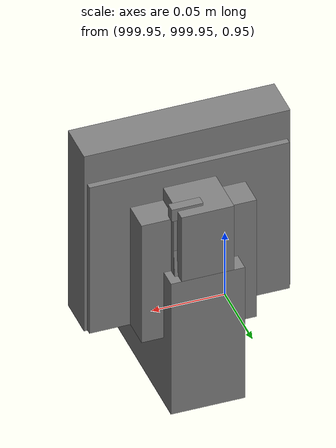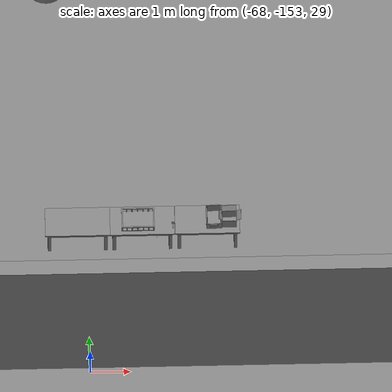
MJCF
<mujoco>
    <option gravity="0.000000000 0.000000000 -9.810000420" timestep="0.0049999999" integrator="implicitfast" density="1.225" viscosity="1.8000001e-05" noslip_iterations="10" iterations="100" sdf_iterations="50">
        <flag multiccd="disable"/>
    </option>
    <size memory="1000M"/>
    <compiler coordinate="local"/>
    <worldbody>
        <light cutoff="30" pos="0 1 1" dir="0 -1 -2"/>
        <light cutoff="30" pos="0 -1 1" dir="0 1 -2"/>
        <body pos="-64.866622925 -149.383972168 30.183746338" euler="89.999984741 89.999946594 0.000000000" name="openloong_gripper_2f85_fix_base_usda_bluebox_01">
            <geom contype="1" conaffinity="1" density="1000" type="box" material="" rgba="0.500000000 0.500000000 0.500000000 1.000000000" solimp="0.899999976 0.949999988 0.001000000" friction="1.000000000 0.005000000 0.000100000" solref="0.020000000 1.000000000" margin="0" condim="3" group="0" pos="0.276580811 0.187225342 0.000068665" quat="0.707106948 0.000077471 0.707106352 0.000077486" size="0.100000001 0.057999998 0.010000000" name="openloong_gripper_2f85_fix_base_usda_geom_534B2EA2_1225_4819_8382_8D506C5E0D89"/>
            <geom contype="1" conaffinity="1" density="1000" type="box" material="" rgba="0.500000000 0.500000000 0.500000000 1.000000000" solimp="0.899999976 0.949999988 0.001000000" friction="1.000000000 0.005000000 0.000100000" solref="0.020000000 1.000000000" margin="0" condim="3" group="0" pos="0.000000000 0.002883911 0.000000000" quat="0.999999881 0.000000000 0.000000000 0.000000000" size="0.254000008 0.003000000 0.172000006" name="openloong_gripper_2f85_fix_base_usda_geom_DB6ADF46_BBAD_4458_92E6_38E39964246D"/>
            <geom contype="1" conaffinity="1" density="1000" type="box" material="" rgba="0.500000000 0.500000000 0.500000000 1.000000000" solimp="0.899999976 0.949999988 0.001000000" friction="1.000000000 0.005000000 0.000100000" solref="0.020000000 1.000000000" margin="0" condim="3" group="0" pos="0.000000000 0.124874115 0.173484802" quat="0.999796331 0.020176515 -0.000000015 0.000000030" size="0.259999990 0.119999997 0.007000000" name="openloong_gripper_2f85_fix_base_usda_geom_0DDF3DCA_1184_4749_9AA7_66B2471DD4E3"/>
            <geom contype="1" conaffinity="1" density="1000" type="box" material="" rgba="0.500000000 0.500000000 0.500000000 1.000000000" solimp="0.899999976 0.949999988 0.001000000" friction="1.000000000 0.005000000 0.000100000" solref="0.020000000 1.000000000" margin="0" condim="3" group="0" pos="0.000000000 0.124874115 -0.173469543" quat="0.999796331 -0.020176545 -0.000000015 0.000000000" size="0.259999990 0.119999997 0.007000000" name="openloong_gripper_2f85_fix_base_usda_geom_396A2CE6_6AB0_46CD_86D7_B0ED3959D2CB"/>
            <geom contype="1" conaffinity="1" density="1000" type="box" material="" rgba="0.500000000 0.500000000 0.500000000 1.000000000" solimp="0.899999976 0.949999988 0.001000000" friction="1.000000000 0.005000000 0.000100000" solref="0.020000000 1.000000000" margin="0" condim="3" group="0" pos="0.000000000 0.214008331 0.188980103" quat="0.999912977 0.013176724 0.000000015 0.000000000" size="0.259999990 0.029999999 0.012500000" name="openloong_gripper_2f85_fix_base_usda_geom_66FF1169_7941_4673_B8E9_6209D3E8D12A"/>
            <geom contype="1" conaffinity="1" density="1000" type="box" material="" rgba="0.500000000 0.500000000 0.500000000 1.000000000" solimp="0.899999976 0.949999988 0.001000000" friction="1.000000000 0.005000000 0.000100000" solref="0.020000000 1.000000000" margin="0" condim="3" group="0" pos="-0.258361816 0.125289917 0.001876831" quat="0.702796936 -0.020792112 0.710783124 0.020769298" size="0.189999998 0.119999997 0.009000000" name="openloong_gripper_2f85_fix_base_usda_geom_297161A5_70B0_40FE_B3C9_74DA6A9DB87A"/>
            <geom contype="1" conaffinity="1" density="1000" type="box" material="" rgba="0.500000000 0.500000000 0.500000000 1.000000000" solimp="0.899999976 0.949999988 0.001000000" friction="1.000000000 0.005000000 0.000100000" solref="0.020000000 1.000000000" margin="0" condim="3" group="0" pos="0.000000000 0.214008331 -0.188980103" quat="0.999912977 -0.013176769 0.000000030 0.000000015" size="0.259999990 0.029999999 0.012500000" name="openloong_gripper_2f85_fix_base_usda_geom_9DBEFC93_3872_4D52_B80D_BD9477F00E1B"/>
            <geom contype="1" conaffinity="1" density="1000" type="box" material="" rgba="0.500000000 0.500000000 0.500000000 1.000000000" solimp="0.899999976 0.949999988 0.001000000" friction="1.000000000 0.005000000 0.000100000" solref="0.020000000 1.000000000" margin="0" condim="3" group="0" pos="-0.276611328 0.187225342 0.000068665" quat="0.707106650 0.000077441 0.707106709 0.000077456" size="0.100000001 0.057999998 0.010000000" name="openloong_gripper_2f85_fix_base_usda_geom_98F87577_851F_4AC7_A6AE_A7908464BD7F"/>
            <geom contype="1" conaffinity="1" density="1000" type="box" material="" rgba="0.500000000 0.500000000 0.500000000 1.000000000" solimp="0.899999976 0.949999988 0.001000000" friction="1.000000000 0.005000000 0.000100000" solref="0.020000000 1.000000000" margin="0" condim="3" group="0" pos="0.258331299 0.125289917 0.001876831" quat="0.702851415 0.018856421 0.710823774 -0.019329369" size="0.189999998 0.119999997 0.009000000" name="openloong_gripper_2f85_fix_base_usda_geom_75EEE76D_EA45_4719_83EA_CBC1585F6440"/>
            <freejoint name="openloong_gripper_2f85_fix_base_usda_bluebox_01_joint"/>
            <site size="0.005000000 0.005000000 0.005000000" rgba="0.500000000 0.500000000 0.500000000 1.000000000" pos="0.000000000 0.000000000 0.000000000" quat="0.999961913 0.008726534 0.000000000 0.000000000" group="0" type="sphere" name="openloong_gripper_2f85_fix_base_usda_bluebox_01site"/>
        </body>
        <body pos="-64.496299744 -149.491867065 30.235729218" euler="0.000000000 0.000000000 89.999946594" name="openloong_gripper_2f85_fix_base_usda_cardboardbox_01">
            <geom contype="1" conaffinity="1" density="1000" type="box" material="" rgba="0.500000000 0.500000000 0.500000000 1.000000000" solimp="0.899999976 0.949999988 0.001000000" friction="1.000000000 0.005000000 0.000100000" solref="0.020000000 1.000000000" margin="0" condim="3" group="0" pos="-0.003166199 -0.004086494 0.005052090" quat="1.000000000 0.000000000 0.000000000 0.000000000" size="0.142499998 0.177500010 0.005000000" name="openloong_gripper_2f85_fix_base_usda_geom_850F6E91_128A_4357_8CBF_64E5352334CE"/>
            <geom contype="1" conaffinity="1" density="1000" type="box" material="" rgba="0.500000000 0.500000000 0.500000000 1.000000000" solimp="0.899999976 0.949999988 0.001000000" friction="1.000000000 0.005000000 0.000100000" solref="0.020000000 1.000000000" margin="0" condim="3" group="0" pos="-0.003166199 0.170316696 0.150570869" quat="1.000000000 0.000000000 0.000000000 0.000000000" size="0.142499998 0.005000000 0.149999991" name="openloong_gripper_2f85_fix_base_usda_geom_D3132189_6D0B_4D09_9647_E46A6E209D16"/>
            <geom contype="1" conaffinity="1" density="1000" type="box" material="" rgba="0.500000000 0.500000000 0.500000000 1.000000000" solimp="0.899999976 0.949999988 0.001000000" friction="1.000000000 0.005000000 0.000100000" solref="0.020000000 1.000000000" margin="0" condim="3" group="0" pos="-0.147399902 -0.005307198 0.150570869" quat="1.000000000 0.000000000 0.000000000 0.000000000" size="0.005000000 0.177500010 0.149999991" name="openloong_gripper_2f85_fix_base_usda_geom_085DBB0C_C15D_4F6E_BB03_476A9B9781BB"/>
            <geom contype="1" conaffinity="1" density="1000" type="box" material="" rgba="0.500000000 0.500000000 0.500000000 1.000000000" solimp="0.899999976 0.949999988 0.001000000" friction="1.000000000 0.005000000 0.000100000" solref="0.020000000 1.000000000" margin="0" condim="3" group="0" pos="0.140275955 -0.005307198 0.150570869" quat="1.000000000 0.000000000 0.000000000 0.000000000" size="0.005000000 0.177500010 0.149999991" name="openloong_gripper_2f85_fix_base_usda_geom_E8AB5873_F806_4B5B_8CBD_9E04730BFC48"/>
            <geom contype="1" conaffinity="1" density="1000" type="box" material="" rgba="0.500000000 0.500000000 0.500000000 1.000000000" solimp="0.899999976 0.949999988 0.001000000" friction="1.000000000 0.005000000 0.000100000" solref="0.020000000 1.000000000" margin="0" condim="3" group="0" pos="-0.003166199 -0.181550980 0.150570869" quat="1.000000000 0.000000000 0.000000000 0.000000000" size="0.142499998 0.005000000 0.149999991" name="openloong_gripper_2f85_fix_base_usda_geom_1B386A13_0F1C_4561_877F_E1C0818BD72E"/>
            <freejoint name="openloong_gripper_2f85_fix_base_usda_cardboardbox_01_joint"/>
            <site size="0.005000000 0.005000000 0.005000000" rgba="0.500000000 0.500000000 0.500000000 1.000000000" pos="0.000000000 0.000000000 0.000000000" quat="0.999961913 0.008726535 0.000000000 0.000000000" group="0" type="sphere" name="openloong_gripper_2f85_fix_base_usda_site_79A25D95_C99F_415B_B509_EB124B2C308B"/>
            <body pos="0.139160156 -0.004048347 0.301930904" euler="-179.999954224 49.383502960 179.999954224" name="openloong_gripper_2f85_fix_base_usda_A1_006">
                <geom contype="1" conaffinity="1" density="1000" type="box" material="" rgba="0.500000000 0.500000000 0.500000000 1.000000000" solimp="0.899999976 0.949999988 0.001000000" friction="1.000000000 0.005000000 0.000100000" solref="0.020000000 1.000000000" margin="0" condim="3" group="0" pos="-0.071587563 0.000009537 0.001745224" quat="0.999999881 0.000000000 0.000000000 0.000000000" size="0.071249999 0.179999992 0.002500000" name="openloong_gripper_2f85_fix_base_usda_geom_B9D7FA85_21D7_4690_A86B_356361955715"/>
                <joint armature="0" stiffness="0.07" damping="0.0099999998" axis="0.000000 1.000000 0.000000" type="hinge" name="openloong_gripper_2f85_fix_base_usda_A1_006"/>
            </body>
            <body pos="-0.145902634 -0.004086494 0.301938057" euler="-180.000000000 -60.000011444 -180.000000000" name="openloong_gripper_2f85_fix_base_usda_A2_006">
                <geom contype="1" conaffinity="1" density="1000" type="box" material="" rgba="0.500000000 0.500000000 0.500000000 1.000000000" solimp="0.899999976 0.949999988 0.001000000" friction="1.000000000 0.005000000 0.000100000" solref="0.020000000 1.000000000" margin="0" condim="3" group="0" pos="0.071268082 0.000009537 0.002717972" quat="0.000002921 0.000000000 -0.000000030 0.999999881" size="0.071249999 0.179999992 0.002500000" name="openloong_gripper_2f85_fix_base_usda_geom_5310CE6E_0355_4140_997F_5F3DF75F592A"/>
                <joint armature="0" stiffness="0.07" damping="0.0099999998" axis="0.000000 1.000000 0.000000" type="hinge" name="openloong_gripper_2f85_fix_base_usda_A2_006"/>
            </body>
            <body pos="-0.003385544 0.175991058 0.301930904" euler="-125.858116150 -0.000004561 0.000002331" name="openloong_gripper_2f85_fix_base_usda_B2_006">
                <geom contype="1" conaffinity="1" density="1000" type="box" material="" rgba="0.500000000 0.500000000 0.500000000 1.000000000" solimp="0.899999976 0.949999988 0.001000000" friction="1.000000000 0.005000000 0.000100000" solref="0.020000000 1.000000000" margin="0" condim="3" group="0" pos="0.000009537 -0.070939064 -0.002470016" quat="0.999614120 0.027776197 -0.000000015 0.000000030" size="0.137500003 0.064999998 0.005000000" name="openloong_gripper_2f85_fix_base_usda_geom_3F207954_8E8B_411A_AEEB_84276DB1FEBB"/>
                <joint armature="0" stiffness="0.07" damping="0.0099999998" axis="1.000000 0.000000 0.000000" type="hinge" name="openloong_gripper_2f85_fix_base_usda_B2_006"/>
            </body>
            <body pos="-0.003385544 -0.184140205 0.301938057" euler="147.805557251 0.000000000 0.000000000" name="openloong_gripper_2f85_fix_base_usda_B1_006">
                <geom contype="1" conaffinity="1" density="1000" type="box" material="" rgba="0.500000000 0.500000000 0.500000000 1.000000000" solimp="0.899999976 0.949999988 0.001000000" friction="1.000000000 0.005000000 0.000100000" solref="0.020000000 1.000000000" margin="0" condim="3" group="0" pos="-0.000028610 0.070202351 -0.002703667" quat="0.999614179 -0.027776167 0.000000000 0.000000000" size="0.137500003 0.064999998 0.005000000" name="openloong_gripper_2f85_fix_base_usda_geom_2B0DC49F_6A41_46B7_A553_5E9DDF08593F"/>
                <joint armature="0" stiffness="0.07" damping="0.0099999998" axis="1.000000 0.000000 0.000000" type="hinge" name="openloong_gripper_2f85_fix_base_usda_B1_006"/>
            </body>
        </body>
        <body pos="-65.882858276 -149.481979370 30.229999542" euler="-64.487716675 0.000000000 0.000000000" name="openloong_gripper_2f85_fix_base_usda_Barcode">
            <geom contype="1" conaffinity="1" density="1000" type="box" material="" rgba="0.500000000 0.500000000 0.500000000 1.000000000" solimp="0.899999976 0.949999988 0.001000000" friction="1.000000000 0.005000000 0.000100000" solref="0.020000000 1.000000000" margin="0" condim="3" group="0" pos="0.000000000 0.013038635 0.001419067" quat="0.000000000 0.000000000 0.000000000 1.000000119" size="0.034000002 0.010000000 0.017999999" name="openloong_gripper_2f85_fix_base_usda_geom_BF5A9A6B_CF1F_418A_95F9_163F4380924D"/>
            <geom contype="1" conaffinity="1" density="1000" type="box" material="" rgba="0.500000000 0.500000000 0.500000000 1.000000000" solimp="0.899999976 0.949999988 0.001000000" friction="1.000000000 0.005000000 0.000100000" solref="0.020000000 1.000000000" margin="0" condim="3" group="0" pos="0.000000000 -0.035301208 -0.007095337" quat="0.000000000 0.000000000 -0.043619365 0.999048233" size="0.028999999 0.010000000 0.020000000" name="openloong_gripper_2f85_fix_base_usda_geom_1594F0A8_E2FD_4AD3_85F1_3AD197AE98E7"/>
            <geom contype="1" conaffinity="1" density="1000" type="box" material="" rgba="0.500000000 0.500000000 0.500000000 1.000000000" solimp="0.899999976 0.949999988 0.001000000" friction="1.000000000 0.005000000 0.000100000" solref="0.020000000 1.000000000" margin="0" condim="3" group="0" pos="0.000000000 -0.043411255 -0.011749268" quat="0.922262907 0.386563420 0.000000000 0.000000000" size="0.026000001 0.010000000 0.020000000" name="openloong_gripper_2f85_fix_base_usda_geom_5C610268_DB73_4893_B0F0_8581A31B21B2"/>
            <geom contype="1" conaffinity="1" density="1000" type="box" material="" rgba="0.500000000 0.500000000 0.500000000 1.000000000" solimp="0.899999976 0.949999988 0.001000000" friction="1.000000000 0.005000000 0.000100000" solref="0.020000000 1.000000000" margin="0" condim="3" group="0" pos="0.000000000 -0.016967773 -0.031860352" quat="0.000000000 0.000000000 0.000000000 1.000000119" size="0.008000000 0.010000000 0.013000000" name="openloong_gripper_2f85_fix_base_usda_geom_BFC5A393_3784_4AAF_B1A1_24EB0ECD6B9E"/>
            <geom contype="1" conaffinity="1" density="1000" type="box" material="" rgba="0.500000000 0.500000000 0.500000000 1.000000000" solimp="0.899999976 0.949999988 0.001000000" friction="1.000000000 0.005000000 0.000100000" solref="0.020000000 1.000000000" margin="0" condim="3" group="0" pos="0.000000000 -0.001869202 0.000312805" quat="0.953716993 0.300705761 0.000000000 0.000000000" size="0.032000002 0.010000000 0.018999999" name="openloong_gripper_2f85_fix_base_usda_geom_535F945D_9A32_4D9E_BF07_BA52FD5C2724"/>
            <geom contype="1" conaffinity="1" density="1000" type="box" material="" rgba="0.500000000 0.500000000 0.500000000 1.000000000" solimp="0.899999976 0.949999988 0.001000000" friction="1.000000000 0.005000000 0.000100000" solref="0.020000000 1.000000000" margin="0" condim="3" group="0" pos="0.000000000 -0.019531250 -0.003173828" quat="0.953716993 0.300705761 0.000000000 0.000000000" size="0.030999999 0.010000000 0.020000000" name="openloong_gripper_2f85_fix_base_usda_geom_2C901E36_E1A4_4FAC_A82A_8D6899246A6E"/>
            <geom contype="1" conaffinity="1" density="1000" type="box" material="" rgba="0.500000000 0.500000000 0.500000000 1.000000000" solimp="0.899999976 0.949999988 0.001000000" friction="1.000000000 0.005000000 0.000100000" solref="0.020000000 1.000000000" margin="0" condim="3" group="0" pos="0.000000000 -0.035301208 -0.007095337" quat="0.953716993 0.300705761 0.000000000 0.000000000" size="0.028999999 0.010000000 0.020000000" name="openloong_gripper_2f85_fix_base_usda_geom_7F26C494_5282_472F_A832_C6F2154A1FF1"/>
            <geom contype="1" conaffinity="1" density="1000" type="box" material="" rgba="0.500000000 0.500000000 0.500000000 1.000000000" solimp="0.899999976 0.949999988 0.001000000" friction="1.000000000 0.005000000 0.000100000" solref="0.020000000 1.000000000" margin="0" condim="3" group="0" pos="0.000000000 -0.042617798 -0.071121216" quat="0.000000000 0.000000000 0.000000000 1.000000119" size="0.013000000 0.021000000 0.059999999" name="openloong_gripper_2f85_fix_base_usda_geom_7CFA3941_4B54_4EEB_A371_ACD844FE0E47"/>
            <freejoint name="openloong_gripper_2f85_fix_base_usda_Barcode_joint"/>
            <site size="0.005000000 0.005000000 0.005000000" rgba="0.500000000 0.500000000 0.500000000 1.000000000" pos="0.000000000 0.000000000 0.000000000" quat="1.000000000 0.000000000 0.000000000 0.000000000" group="0" type="sphere" name="openloong_gripper_2f85_fix_base_usda_Barcode_site"/>
        </body>
        <body pos="-66.745018005 -149.392349243 30.184000015" euler="0.000000000 0.000000000 89.999946594" name="[22332193645221]_Basket_01">
            <geom contype="1" conaffinity="1" density="1000" type="box" material="" rgba="0.500000000 0.500000000 0.500000000 1.000000000" solimp="0.899999976 0.949999988 0.001000000" friction="1.000000000 0.005000000 0.000100000" solref="0.020000000 1.000000000" margin="0" condim="3" group="0" pos="-0.052425385 0.389207840 0.089787483" quat="0.707107008 0.000000000 0.000000000 0.707106411" size="0.014249999 0.014249999 0.059999999" name="[22332193645221]_geom_014501E4_4CD9_455A_8CDD_59BBBC0074A5"/>
            <geom contype="1" conaffinity="1" density="1000" type="box" material="" rgba="0.500000000 0.500000000 0.500000000 1.000000000" solimp="0.899999976 0.949999988 0.001000000" friction="1.000000000 0.005000000 0.000100000" solref="0.020000000 1.000000000" margin="0" condim="3" group="0" pos="0.264015198 -0.133043289 0.089787483" quat="0.707107008 0.000000000 0.000000000 0.707106411" size="0.014249999 0.014249999 0.059999999" name="[22332193645221]_geom_B73424B0_E6FC_4823_9178_1B768DD3BB86"/>
            <geom contype="1" conaffinity="1" density="1000" type="box" material="" rgba="0.500000000 0.500000000 0.500000000 1.000000000" solimp="0.899999976 0.949999988 0.001000000" friction="1.000000000 0.005000000 0.000100000" solref="0.020000000 1.000000000" margin="0" condim="3" group="0" pos="-0.264015198 -0.265548706 0.089793205" quat="0.707107008 0.000000000 0.000000000 0.707106411" size="0.014249999 0.014249999 0.059999999" name="[22332193645221]_geom_29F4C0AA_33F3_4593_B863_C42139BDC7D0"/>
            <geom contype="1" conaffinity="1" density="1000" type="box" material="" rgba="0.500000000 0.500000000 0.500000000 1.000000000" solimp="0.899999976 0.949999988 0.001000000" friction="1.000000000 0.005000000 0.000100000" solref="0.020000000 1.000000000" margin="0" condim="3" group="0" pos="-0.160263062 -0.389322281 0.089793205" quat="0.707107008 0.000000000 0.000000000 0.707106411" size="0.014249999 0.014249999 0.059999999" name="[22332193645221]_geom_FDCF5D1B_57A8_49E3_BE4A_EFBDDD79240F"/>
            <geom contype="1" conaffinity="1" density="1000" type="box" material="" rgba="0.500000000 0.500000000 0.500000000 1.000000000" solimp="0.899999976 0.949999988 0.001000000" friction="1.000000000 0.005000000 0.000100000" solref="0.020000000 1.000000000" margin="0" condim="3" group="0" pos="0.162265778 -0.389322281 0.089787483" quat="0.707107008 0.000000000 0.000000000 0.707106411" size="0.014249999 0.014249999 0.059999999" name="[22332193645221]_geom_D2DB4154_47CC_4679_A42B_5657D23C0542"/>
            <geom contype="1" conaffinity="1" density="1000" type="box" material="" rgba="0.500000000 0.500000000 0.500000000 1.000000000" solimp="0.899999976 0.949999988 0.001000000" friction="1.000000000 0.005000000 0.000100000" solref="0.020000000 1.000000000" margin="0" condim="3" group="0" pos="0.264015198 0.389207840 0.089787483" quat="0.707107008 0.000000000 0.000000000 0.707106411" size="0.014249999 0.014249999 0.059999999" name="[22332193645221]_geom_FAAB7809_183E_48D9_A304_1F1433079F96"/>
            <geom contype="1" conaffinity="1" density="1000" type="box" material="" rgba="0.500000000 0.500000000 0.500000000 1.000000000" solimp="0.899999976 0.949999988 0.001000000" friction="1.000000000 0.005000000 0.000100000" solref="0.020000000 1.000000000" margin="0" condim="3" group="0" pos="-0.264015198 -0.133043289 0.089793205" quat="0.707107008 0.000000000 0.000000000 0.707106411" size="0.014249999 0.014249999 0.059999999" name="[22332193645221]_geom_757EB444_BB30_4825_8C0D_4E8EDC0709A4"/>
            <geom contype="1" conaffinity="1" density="1000" type="box" material="" rgba="0.500000000 0.500000000 0.500000000 1.000000000" solimp="0.899999976 0.949999988 0.001000000" friction="1.000000000 0.005000000 0.000100000" solref="0.020000000 1.000000000" margin="0" condim="3" group="0" pos="-0.264026642 0.269256592 0.089793205" quat="0.707107008 0.000000000 0.000000000 0.707106411" size="0.014249999 0.014249999 0.059999999" name="[22332193645221]_geom_77536B22_6509_46AE_9618_6E7746AE63FA"/>
            <geom contype="1" conaffinity="1" density="1000" type="box" material="" rgba="0.500000000 0.500000000 0.500000000 1.000000000" solimp="0.899999976 0.949999988 0.001000000" friction="1.000000000 0.005000000 0.000100000" solref="0.020000000 1.000000000" margin="0" condim="3" group="0" pos="0.054462433 0.389207840 0.089787483" quat="0.707107008 0.000000000 0.000000000 0.707106411" size="0.014249999 0.014249999 0.059999999" name="[22332193645221]_geom_4C03C4A2_E5A3_450A_A8A6_ACCF34048CA8"/>
            <geom contype="1" conaffinity="1" density="1000" type="box" material="" rgba="0.500000000 0.500000000 0.500000000 1.000000000" solimp="0.899999976 0.949999988 0.001000000" friction="1.000000000 0.005000000 0.000100000" solref="0.020000000 1.000000000" margin="0" condim="3" group="0" pos="0.054462433 -0.389322281 0.089787483" quat="0.707107008 0.000000000 0.000000000 0.707106411" size="0.014249999 0.014249999 0.059999999" name="[22332193645221]_geom_593111C0_066A_477F_BDBF_B936B66DC1DD"/>
            <geom contype="1" conaffinity="1" density="1000" type="box" material="" rgba="0.500000000 0.500000000 0.500000000 1.000000000" solimp="0.899999976 0.949999988 0.001000000" friction="1.000000000 0.005000000 0.000100000" solref="0.020000000 1.000000000" margin="0" condim="3" group="0" pos="0.264015198 0.269256592 0.089793205" quat="0.707107008 0.000000000 0.000000000 0.707106411" size="0.014249999 0.014249999 0.059999999" name="[22332193645221]_geom_D820CEBD_2BE1_492A_A793_92BB7413500E"/>
            <geom contype="1" conaffinity="1" density="1000" type="box" material="" rgba="0.500000000 0.500000000 0.500000000 1.000000000" solimp="0.899999976 0.949999988 0.001000000" friction="1.000000000 0.005000000 0.000100000" solref="0.020000000 1.000000000" margin="0" condim="3" group="0" pos="0.264015198 -0.389322281 0.089787483" quat="0.707107008 0.000000000 0.000000000 0.707106411" size="0.014249999 0.014249999 0.059999999" name="[22332193645221]_geom_1A8D6A63_4BC8_43EF_8A17_6D1DF46FD937"/>
            <geom contype="1" conaffinity="1" density="1000" type="box" material="" rgba="0.500000000 0.500000000 0.500000000 1.000000000" solimp="0.899999976 0.949999988 0.001000000" friction="1.000000000 0.005000000 0.000100000" solref="0.020000000 1.000000000" margin="0" condim="3" group="0" pos="0.000000000 0.000000000 0.015998840" quat="0.707107008 0.000000000 0.000000000 0.707106411" size="0.403499991 0.279000014 0.015750000" name="[22332193645221]_geom_27061A9F_72CC_4860_A103_072B585BFA67"/>
            <geom contype="1" conaffinity="1" density="1000" type="box" material="" rgba="0.500000000 0.500000000 0.500000000 1.000000000" solimp="0.899999976 0.949999988 0.001000000" friction="1.000000000 0.005000000 0.000100000" solref="0.020000000 1.000000000" margin="0" condim="3" group="0" pos="0.000000000 -0.389476776 0.163619041" quat="0.707107008 0.000000000 0.000000000 0.707106411" size="0.015000000 0.277500004 0.015750000" name="[22332193645221]_geom_CA4ACE1B_F85B_461D_90C6_5416C1A828F4"/>
            <geom contype="1" conaffinity="1" density="1000" type="box" material="" rgba="0.500000000 0.500000000 0.500000000 1.000000000" solimp="0.899999976 0.949999988 0.001000000" friction="1.000000000 0.005000000 0.000100000" solref="0.020000000 1.000000000" margin="0" condim="3" group="0" pos="0.162265778 0.389207840 0.089787483" quat="0.707107008 0.000000000 0.000000000 0.707106411" size="0.014249999 0.014249999 0.059999999" name="[22332193645221]_geom_9CB1F307_7ADA_4CE9_AF40_2D7AE20CE3FD"/>
            <geom contype="1" conaffinity="1" density="1000" type="box" material="" rgba="0.500000000 0.500000000 0.500000000 1.000000000" solimp="0.899999976 0.949999988 0.001000000" friction="1.000000000 0.005000000 0.000100000" solref="0.020000000 1.000000000" margin="0" condim="3" group="0" pos="0.000000000 0.389471054 0.163619041" quat="0.707107008 0.000000000 0.000000000 0.707106411" size="0.015000000 0.277500004 0.015750000" name="[22332193645221]_geom_14D3806E_61C9_46F5_A212_8E88738F6C2C"/>
            <geom contype="1" conaffinity="1" density="1000" type="box" material="" rgba="0.500000000 0.500000000 0.500000000 1.000000000" solimp="0.899999976 0.949999988 0.001000000" friction="1.000000000 0.005000000 0.000100000" solref="0.020000000 1.000000000" margin="0" condim="3" group="0" pos="-0.263511658 0.000000000 0.163619041" quat="0.707107008 0.000000000 0.000000000 0.707106411" size="0.403499991 0.015000000 0.015750000" name="[22332193645221]_geom_323D7ADC_3FE1_453F_9FF9_5039695A8138"/>
            <geom contype="1" conaffinity="1" density="1000" type="box" material="" rgba="0.500000000 0.500000000 0.500000000 1.000000000" solimp="0.899999976 0.949999988 0.001000000" friction="1.000000000 0.005000000 0.000100000" solref="0.020000000 1.000000000" margin="0" condim="3" group="0" pos="-0.264015198 0.141334534 0.089793205" quat="0.707107008 0.000000000 0.000000000 0.707106411" size="0.014249999 0.014249999 0.059999999" name="[22332193645221]_geom_01034A05_0976_4D81_9AF6_60077C069759"/>
            <geom contype="1" conaffinity="1" density="1000" type="box" material="" rgba="0.500000000 0.500000000 0.500000000 1.000000000" solimp="0.899999976 0.949999988 0.001000000" friction="1.000000000 0.005000000 0.000100000" solref="0.020000000 1.000000000" margin="0" condim="3" group="0" pos="0.264015198 -0.265548706 0.089787483" quat="0.707107008 0.000000000 0.000000000 0.707106411" size="0.014249999 0.014249999 0.059999999" name="[22332193645221]_geom_CFAD8D25_E351_4721_AC4A_5695A7858768"/>
            <geom contype="1" conaffinity="1" density="1000" type="box" material="" rgba="0.500000000 0.500000000 0.500000000 1.000000000" solimp="0.899999976 0.949999988 0.001000000" friction="1.000000000 0.005000000 0.000100000" solref="0.020000000 1.000000000" margin="0" condim="3" group="0" pos="-0.160263062 0.389207840 0.089787483" quat="0.707107008 0.000000000 0.000000000 0.707106411" size="0.014249999 0.014249999 0.059999999" name="[22332193645221]_geom_ACE91D87_26C7_4B8B_899B_CB11D55E5244"/>
            <geom contype="1" conaffinity="1" density="1000" type="box" material="" rgba="0.500000000 0.500000000 0.500000000 1.000000000" solimp="0.899999976 0.949999988 0.001000000" friction="1.000000000 0.005000000 0.000100000" solref="0.020000000 1.000000000" margin="0" condim="3" group="0" pos="-0.052425385 -0.389322281 0.089787483" quat="0.707107008 0.000000000 0.000000000 0.707106411" size="0.014249999 0.014249999 0.059999999" name="[22332193645221]_geom_2CB57E67_CB1D_48F7_A3CA_9AF2876BE2D3"/>
            <geom contype="1" conaffinity="1" density="1000" type="box" material="" rgba="0.500000000 0.500000000 0.500000000 1.000000000" solimp="0.899999976 0.949999988 0.001000000" friction="1.000000000 0.005000000 0.000100000" solref="0.020000000 1.000000000" margin="0" condim="3" group="0" pos="-0.264026642 -0.389322281 0.089793205" quat="0.707107008 0.000000000 0.000000000 0.707106411" size="0.014249999 0.014249999 0.059999999" name="[22332193645221]_geom_E8C98771_9F7B_454F_BD28_788F6F23DA28"/>
            <geom contype="1" conaffinity="1" density="1000" type="box" material="" rgba="0.500000000 0.500000000 0.500000000 1.000000000" solimp="0.899999976 0.949999988 0.001000000" friction="1.000000000 0.005000000 0.000100000" solref="0.020000000 1.000000000" margin="0" condim="3" group="0" pos="0.264015198 0.141334534 0.089787483" quat="0.707107008 0.000000000 0.000000000 0.707106411" size="0.014249999 0.014249999 0.059999999" name="[22332193645221]_geom_7F5274EE_56DA_4BFE_9C16_287251C49610"/>
            <geom contype="1" conaffinity="1" density="1000" type="box" material="" rgba="0.500000000 0.500000000 0.500000000 1.000000000" solimp="0.899999976 0.949999988 0.001000000" friction="1.000000000 0.005000000 0.000100000" solref="0.020000000 1.000000000" margin="0" condim="3" group="0" pos="-0.264015198 0.389207840 0.089793205" quat="0.707107008 0.000000000 0.000000000 0.707106411" size="0.014249999 0.014249999 0.059999999" name="[22332193645221]_geom_3C9890B6_35DF_4985_83B0_65A5ECED2C5F"/>
            <geom contype="1" conaffinity="1" density="1000" type="box" material="" rgba="0.500000000 0.500000000 0.500000000 1.000000000" solimp="0.899999976 0.949999988 0.001000000" friction="1.000000000 0.005000000 0.000100000" solref="0.020000000 1.000000000" margin="0" condim="3" group="0" pos="0.264015198 0.004480362 0.089787483" quat="0.707107008 0.000000000 0.000000000 0.707106411" size="0.014249999 0.014249999 0.059999999" name="[22332193645221]_geom_CD73785B_E025_417D_89F0_85E981454E0A"/>
            <geom contype="1" conaffinity="1" density="1000" type="box" material="" rgba="0.500000000 0.500000000 0.500000000 1.000000000" solimp="0.899999976 0.949999988 0.001000000" friction="1.000000000 0.005000000 0.000100000" solref="0.020000000 1.000000000" margin="0" condim="3" group="0" pos="0.263694763 -0.000011444 0.163619041" quat="0.707107008 0.000000000 0.000000000 0.707106411" size="0.403499991 0.015000000 0.015750000" name="[22332193645221]_geom_58D4AD85_E5C4_46E3_AE6D_D09A6B99C5D3"/>
            <geom contype="1" conaffinity="1" density="1000" type="box" material="" rgba="0.500000000 0.500000000 0.500000000 1.000000000" solimp="0.899999976 0.949999988 0.001000000" friction="1.000000000 0.005000000 0.000100000" solref="0.020000000 1.000000000" margin="0" condim="3" group="0" pos="-0.264015198 0.004480362 0.089793205" quat="0.707107008 0.000000000 0.000000000 0.707106411" size="0.014249999 0.014249999 0.059999999" name="[22332193645221]_geom_DA400D8D_8506_468B_8791_9024F7A3089C"/>
            <freejoint name="[22332193645221]_joint_DF6B8203_9F20_46F0_807E_A950ABD85680"/>
        </body>
        <body pos="0.000000000 0.000000000 0.000000000" euler="0.000000000 0.000000000 0.000000000" name="Static Objects_Static Objects">
            <geom contype="1" conaffinity="1" density="1000" type="box" material="" rgba="0.500000000 0.500000000 0.500000000 1.000000000" solimp="0.899999976 0.949999988 0.001000000" friction="1.000000000 0.005000000 0.000100000" solref="0.020000000 1.000000000" margin="0" condim="3" group="0" pos="-67.544113159 -149.365814209 29.727830887" quat="0.500000417 0.499999970 0.499999553 0.499999970" size="0.381000012 0.319999993 0.041000001" name="Static Objects_geom_6C561291_515B_40AF_AD64_FD9D9C9FCF01"/>
            <geom contype="1" conaffinity="1" density="1000" type="box" material="" rgba="0.500000000 0.500000000 0.500000000 1.000000000" solimp="0.899999976 0.949999988 0.001000000" friction="1.000000000 0.005000000 0.000100000" solref="0.020000000 1.000000000" margin="0" condim="3" group="0" pos="-68.239501953 -149.365814209 30.086868286" quat="0.500000417 0.499999970 0.499999553 0.499999970" size="0.370999992 0.039500002 0.745000005" name="Static Objects_geom_F173830E_1A5D_4B44_91DB_8A7C8F3BEA5F"/>
            <geom contype="1" conaffinity="1" density="1000" type="box" material="" rgba="0.500000000 0.500000000 0.500000000 1.000000000" solimp="0.899999976 0.949999988 0.001000000" friction="1.000000000 0.005000000 0.000100000" solref="0.020000000 1.000000000" margin="0" condim="3" group="0" pos="-68.239501953 -149.365814209 30.147235870" quat="0.500000417 0.499999970 0.499999553 0.499999970" size="0.400000006 0.022000000 0.800000012" name="Static Objects_geom_14169C37_2966_461A_9BC6_83CB6B01152A"/>
            <geom contype="1" conaffinity="1" density="1000" type="box" material="" rgba="0.500000000 0.500000000 0.500000000 1.000000000" solimp="0.899999976 0.949999988 0.001000000" friction="1.000000000 0.005000000 0.000100000" solref="0.020000000 1.000000000" margin="0" condim="3" group="0" pos="-68.934890747 -149.365814209 29.727830887" quat="0.500000417 0.499999970 0.499999553 0.499999970" size="0.381000012 0.319999993 0.041000001" name="Static Objects_geom_6F2C81AB_DE8F_4B0C_83CD_A78DA633CCBA"/>
            <geom contype="1" conaffinity="1" density="1000" type="box" material="" rgba="0.500000000 0.500000000 0.500000000 1.000000000" solimp="0.899999976 0.949999988 0.001000000" friction="1.000000000 0.005000000 0.000100000" solref="0.020000000 1.000000000" margin="0" condim="3" group="0" pos="-68.239501953 -149.365814209 29.561563492" quat="0.500000417 0.499999970 0.499999553 0.499999970" size="0.020000000 0.022000000 0.660000026" name="Static Objects_geom_8493E529_0AF0_41FB_B3C8_075420897D88"/>
            <geom contype="1" conaffinity="1" density="1000" type="box" material="" rgba="0.500000000 0.500000000 0.500000000 1.000000000" solimp="0.899999976 0.949999988 0.001000000" friction="1.000000000 0.005000000 0.000100000" solref="0.020000000 1.000000000" margin="0" condim="3" group="0" pos="-65.945671082 -149.365814209 29.727830887" quat="0.500000417 0.499999970 0.499999553 0.499999970" size="0.381000012 0.319999993 0.041000001" name="Static Objects_geom_4423C5A7_868E_49C8_8D93_93CCD5AC3A82"/>
            <geom contype="1" conaffinity="1" density="1000" type="box" material="" rgba="0.500000000 0.500000000 0.500000000 1.000000000" solimp="0.899999976 0.949999988 0.001000000" friction="1.000000000 0.005000000 0.000100000" solref="0.020000000 1.000000000" margin="0" condim="3" group="0" pos="-66.641059875 -149.365814209 30.086868286" quat="0.500000417 0.499999970 0.499999553 0.499999970" size="0.370999992 0.039500002 0.745000005" name="Static Objects_geom_80AB7448_F8F9_4EC4_AA52_D48C4F22D3DD"/>
            <geom contype="1" conaffinity="1" density="1000" type="box" material="" rgba="0.500000000 0.500000000 0.500000000 1.000000000" solimp="0.899999976 0.949999988 0.001000000" friction="1.000000000 0.005000000 0.000100000" solref="0.020000000 1.000000000" margin="0" condim="3" group="0" pos="-66.641059875 -149.365814209 30.147235870" quat="0.500000417 0.499999970 0.499999553 0.499999970" size="0.400000006 0.022000000 0.800000012" name="Static Objects_geom_36FBB33A_4473_4F4D_8642_FE3849CC8994"/>
            <geom contype="1" conaffinity="1" density="1000" type="box" material="" rgba="0.500000000 0.500000000 0.500000000 1.000000000" solimp="0.899999976 0.949999988 0.001000000" friction="1.000000000 0.005000000 0.000100000" solref="0.020000000 1.000000000" margin="0" condim="3" group="0" pos="-67.336448669 -149.365814209 29.727830887" quat="0.500000417 0.499999970 0.499999553 0.499999970" size="0.381000012 0.319999993 0.041000001" name="Static Objects_geom_DDEE3DBE_EAAB_444D_ACB5_D3BF0E06A54E"/>
            <geom contype="1" conaffinity="1" density="1000" type="box" material="" rgba="0.500000000 0.500000000 0.500000000 1.000000000" solimp="0.899999976 0.949999988 0.001000000" friction="1.000000000 0.005000000 0.000100000" solref="0.020000000 1.000000000" margin="0" condim="3" group="0" pos="-66.641059875 -149.365814209 29.561563492" quat="0.500000417 0.499999970 0.499999553 0.499999970" size="0.020000000 0.022000000 0.660000026" name="Static Objects_geom_E0A1AFFE_846B_4BC1_9AC0_0873959DAEDF"/>
            <geom contype="1" conaffinity="1" density="1000" type="box" material="" rgba="0.500000000 0.500000000 0.500000000 1.000000000" solimp="0.899999976 0.949999988 0.001000000" friction="1.000000000 0.005000000 0.000100000" solref="0.020000000 1.000000000" margin="0" condim="3" group="0" pos="-64.338577271 -149.365814209 29.727830887" quat="0.500000417 0.499999970 0.499999553 0.499999970" size="0.381000012 0.319999993 0.041000001" name="Static Objects_geom_C43C859B_A2FD_4291_8533_3224247D5F44"/>
            <geom contype="1" conaffinity="1" density="1000" type="box" material="" rgba="0.500000000 0.500000000 0.500000000 1.000000000" solimp="0.899999976 0.949999988 0.001000000" friction="1.000000000 0.005000000 0.000100000" solref="0.020000000 1.000000000" margin="0" condim="3" group="0" pos="-65.033966064 -149.365814209 30.086868286" quat="0.500000417 0.499999970 0.499999553 0.499999970" size="0.370999992 0.039500002 0.745000005" name="Static Objects_geom_2EA7DA73_F7F3_4B46_93AD_D4E384EDF36D"/>
            <geom contype="1" conaffinity="1" density="1000" type="box" material="" rgba="0.500000000 0.500000000 0.500000000 1.000000000" solimp="0.899999976 0.949999988 0.001000000" friction="1.000000000 0.005000000 0.000100000" solref="0.020000000 1.000000000" margin="0" condim="3" group="0" pos="-65.033966064 -149.365814209 30.147235870" quat="0.500000417 0.499999970 0.499999553 0.499999970" size="0.400000006 0.022000000 0.800000012" name="Static Objects_geom_B949AD60_3969_4902_A85A_3972704C450B"/>
            <geom contype="1" conaffinity="1" density="1000" type="box" material="" rgba="0.500000000 0.500000000 0.500000000 1.000000000" solimp="0.899999976 0.949999988 0.001000000" friction="1.000000000 0.005000000 0.000100000" solref="0.020000000 1.000000000" margin="0" condim="3" group="0" pos="-65.729354858 -149.365814209 29.727830887" quat="0.500000417 0.499999970 0.499999553 0.499999970" size="0.381000012 0.319999993 0.041000001" name="Static Objects_geom_00E08FB8_2DAC_49FE_A7EB_E5BB57D2AD6B"/>
            <geom contype="1" conaffinity="1" density="1000" type="box" material="" rgba="0.500000000 0.500000000 0.500000000 1.000000000" solimp="0.899999976 0.949999988 0.001000000" friction="1.000000000 0.005000000 0.000100000" solref="0.020000000 1.000000000" margin="0" condim="3" group="0" pos="-65.033966064 -149.365814209 29.561563492" quat="0.500000417 0.499999970 0.499999553 0.499999970" size="0.020000000 0.022000000 0.660000026" name="Static Objects_geom_198C7BA2_874D_4B18_B093_11D39BA8C9D1"/>
            <geom contype="1" conaffinity="1" density="1000" type="box" material="" rgba="0.500000000 0.500000000 0.500000000 1.000000000" solimp="0.899999976 0.949999988 0.001000000" friction="1.000000000 0.005000000 0.000100000" solref="0.020000000 1.000000000" margin="0" condim="3" group="0" pos="-61.754566193 -137.853729248 33.906845093" quat="0.707107067 0.000000000 0.000000000 0.707106471" size="0.759999990 0.759999990 4.500000000" name="Static Objects_geom_EF278FEF_4DFD_4207_8ADF_30D53EF46867"/>
            <geom contype="1" conaffinity="1" density="1000" type="box" material="" rgba="0.500000000 0.500000000 0.500000000 1.000000000" solimp="0.899999976 0.949999988 0.001000000" friction="1.000000000 0.005000000 0.000100000" solref="0.020000000 1.000000000" margin="0" condim="3" group="0" pos="-57.511135101 -144.927108765 31.707921982" quat="1.000000000 0.000000000 0.000000000 0.000000000" size="0.200000003 8.000000000 2.299999952" name="Static Objects_geom_2BCE5D15_8306_47A5_A61D_445667202785"/>
            <geom contype="1" conaffinity="1" density="1000" type="box" material="" rgba="0.500000000 0.500000000 0.500000000 1.000000000" solimp="0.899999976 0.949999988 0.001000000" friction="1.000000000 0.005000000 0.000100000" solref="0.020000000 1.000000000" margin="0" condim="3" group="0" pos="-80.517646790 -157.574050903 31.688196182" quat="0.707107067 0.000000000 0.000000000 0.707106471" size="0.600000024 0.600000024 2.299999952" name="Static Objects_geom_E3414071_5F37_4217_9850_654F6DF7DFB1"/>
            <geom contype="1" conaffinity="1" density="1000" type="box" material="" rgba="0.500000000 0.500000000 0.500000000 1.000000000" solimp="0.899999976 0.949999988 0.001000000" friction="1.000000000 0.005000000 0.000100000" solref="0.020000000 1.000000000" margin="0" condim="3" group="0" pos="-80.711044312 -147.414932251 31.666158676" quat="1.000000000 0.000000000 0.000000000 0.000000000" size="0.200000003 10.000000000 2.299999952" name="Static Objects_geom_013AC157_D55E_471A_BD76_F19E92A42A33"/>
            <geom contype="1" conaffinity="1" density="1000" type="box" material="" rgba="0.500000000 0.500000000 0.500000000 1.000000000" solimp="0.899999976 0.949999988 0.001000000" friction="1.000000000 0.005000000 0.000100000" solref="0.020000000 1.000000000" margin="0" condim="3" group="0" pos="-57.687217712 -137.434692383 31.688196182" quat="0.707107067 0.000000000 0.000000000 0.707106471" size="0.600000024 0.600000024 2.299999952" name="Static Objects_geom_F0AF0D2C_6EF0_45EE_9834_208F0F3C9E55"/>
            <geom contype="1" conaffinity="1" density="1000" type="box" material="" rgba="0.500000000 0.500000000 0.500000000 1.000000000" solimp="0.899999976 0.949999988 0.001000000" friction="1.000000000 0.005000000 0.000100000" solref="0.020000000 1.000000000" margin="0" condim="3" group="0" pos="-69.537033081 -140.263229370 31.714921951" quat="0.707107067 0.000000000 0.000000000 0.707106471" size="0.759999990 4.500000000 2.299999952" name="Static Objects_geom_EAE971F8_A43A_4668_9AD9_7A090AE69AE1"/>
            <geom contype="1" conaffinity="1" density="1000" type="box" material="" rgba="0.500000000 0.500000000 0.500000000 1.000000000" solimp="0.899999976 0.949999988 0.001000000" friction="1.000000000 0.005000000 0.000100000" solref="0.020000000 1.000000000" margin="0" condim="3" group="0" pos="-80.073638916 -137.853713989 33.906845093" quat="0.707107067 0.000000000 0.000000000 0.707106471" size="0.759999990 0.759999990 4.500000000" name="Static Objects_geom_1BDA6032_D942_451E_A53F_E9AC5CC31413"/>
            <geom contype="1" conaffinity="1" density="1000" type="box" material="" rgba="0.500000000 0.500000000 0.500000000 1.000000000" solimp="0.899999976 0.949999988 0.001000000" friction="1.000000000 0.005000000 0.000100000" solref="0.020000000 1.000000000" margin="0" condim="3" group="0" pos="-73.406707764 -155.734664917 31.707921982" quat="1.000000000 0.000000000 0.000000000 0.000000000" size="0.200000003 3.000000000 2.299999952" name="Static Objects_geom_3FC050D1_1FCC_4309_A3AA_CF501DDE55F1"/>
            <geom contype="1" conaffinity="1" density="1000" type="box" material="" rgba="0.500000000 0.500000000 0.500000000 1.000000000" solimp="0.899999976 0.949999988 0.001000000" friction="1.000000000 0.005000000 0.000100000" solref="0.020000000 1.000000000" margin="0" condim="3" group="0" pos="-68.497543335 -137.448257446 31.707921982" quat="0.707107067 0.000000000 0.000000000 0.707106471" size="0.200000003 14.000000000 2.299999952" name="Static Objects_geom_EF7421A0_0620_4EAE_9754_1FE48C7EFA0A"/>
            <geom contype="1" conaffinity="1" density="1000" type="cylinder" material="" rgba="0.500000000 0.500000000 0.500000000 1.000000000" solimp="0.899999976 0.949999988 0.001000000" friction="1.000000000 0.005000000 0.000100000" solref="0.020000000 1.000000000" margin="0" condim="3" group="0" pos="-68.868522644 -142.134506226 31.711090088" quat="0.707107067 0.000000000 0.000000000 0.707106471" size="0.509999990 2.299999952 1.000000000" name="Static Objects_geom_A6DB1941_6C78_4C65_8753_A5E2515F438F"/>
            <geom contype="1" conaffinity="1" density="1000" type="plane" material="" rgba="0.500000000 0.500000000 0.500000000 1.000000000" solimp="0.899999976 0.949999988 0.001000000" friction="1.000000000 0.005000000 0.000100000" solref="0.020000000 1.000000000" margin="0" condim="3" group="0" pos="-72.873703003 -147.131927490 29.409669876" quat="1.000000000 0.000000000 0.000000000 0.000000000" size="18.000000000 14.000000000 1.000000000" name="Static Objects_geom_F376196D_5771_4330_9B34_3506BF57EA43"/>
            <geom contype="1" conaffinity="1" density="1000" type="box" material="" rgba="0.500000000 0.500000000 0.500000000 1.000000000" solimp="0.899999976 0.949999988 0.001000000" friction="1.000000000 0.005000000 0.000100000" solref="0.020000000 1.000000000" margin="0" condim="3" group="0" pos="-79.943580627 -157.782272339 31.707921982" quat="0.707107067 0.000000000 0.000000000 0.707106471" size="0.200000003 7.000000000 2.299999952" name="Static Objects_geom_5940385C_0FB6_432C_853F_78FF278097B9"/>
            <geom contype="1" conaffinity="1" density="1000" type="box" material="" rgba="0.500000000 0.500000000 0.500000000 1.000000000" solimp="0.899999976 0.949999988 0.001000000" friction="1.000000000 0.005000000 0.000100000" solref="0.020000000 1.000000000" margin="0" condim="3" group="0" pos="-65.421028137 -152.903442383 31.707921982" quat="0.707107067 0.000000000 0.000000000 0.707106471" size="0.200000003 7.800000191 2.299999952" name="Static Objects_geom_92A363EF_ED63_4FC8_89F3_B50A4E31151C"/>
            <geom contype="1" conaffinity="1" density="1000" type="box" material="" rgba="0.500000000 0.500000000 0.500000000 1.000000000" solimp="0.899999976 0.949999988 0.001000000" friction="1.000000000 0.005000000 0.000100000" solref="0.020000000 1.000000000" margin="0" condim="3" group="0" pos="-74.776908875 -149.964416504 31.688196182" quat="1.000000000 0.000000000 0.000000000 0.000000000" size="0.600000024 0.409999996 2.299999952" name="Static Objects_geom_0EAE4E2D_790C_47B9_B7B3_54E921B296DE"/>
            <geom contype="1" conaffinity="1" density="1000" type="cylinder" material="" rgba="0.500000000 0.500000000 0.500000000 1.000000000" solimp="0.899999976 0.949999988 0.001000000" friction="1.000000000 0.005000000 0.000100000" solref="0.020000000 1.000000000" margin="0" condim="3" group="0" pos="-60.161884308 -142.134506226 31.711090088" quat="0.707107067 0.000000000 0.000000000 0.707106471" size="0.509999990 2.299999952 1.000000000" name="Static Objects_geom_6A71E4F8_42BC_4686_85B3_B482D07F3773"/>
            <geom contype="1" conaffinity="1" density="1000" type="cylinder" material="" rgba="0.500000000 0.500000000 0.500000000 1.000000000" solimp="0.899999976 0.949999988 0.001000000" friction="1.000000000 0.005000000 0.000100000" solref="0.020000000 1.000000000" margin="0" condim="3" group="0" pos="-75.382453918 -149.963455200 31.711090088" quat="0.707107067 0.000000000 0.000000000 0.707106471" size="0.409999996 2.299999952 1.000000000" name="Static Objects_geom_8531AC2A_0C05_4D12_A03D_811B90D82306"/>
            <geom contype="1" conaffinity="1" density="1000" type="cylinder" material="" rgba="0.500000000 0.500000000 0.500000000 1.000000000" solimp="0.899999976 0.949999988 0.001000000" friction="1.000000000 0.005000000 0.000100000" solref="0.020000000 1.000000000" margin="0" condim="3" group="0" pos="-74.154960632 -149.963455200 31.711090088" quat="0.707107067 0.000000000 0.000000000 0.707106471" size="0.409999996 2.299999952 1.000000000" name="Static Objects_geom_9FBA99AE_58B5_46F8_86D0_01957440F8AF"/>
            <geom contype="1" conaffinity="1" density="1000" type="cylinder" material="" rgba="0.500000000 0.500000000 0.500000000 1.000000000" solimp="0.899999976 0.949999988 0.001000000" friction="1.000000000 0.005000000 0.000100000" solref="0.020000000 1.000000000" margin="0" condim="3" group="0" pos="-77.566612244 -142.134506226 31.711090088" quat="0.707107067 0.000000000 0.000000000 0.707106471" size="0.509999990 2.299999952 1.000000000" name="Static Objects_geom_757FC2E2_4896_4E2F_A6C3_FB4A1C409A36"/>
        </body>
        <body pos="-65.922500610 -148.824645996 31.162584305" euler="-38.852012634 -29.446279526 -9.879738808" mocap="true" name="spotlight2_SpotLight"/>
        <body pos="1000.000000000 999.999938965 1.000000000" euler="0.000000000 0.000000000 180.000000000" name="openloong_gripper_2f85_fix_base_usda_intelcore_i5">
            <geom contype="1" conaffinity="1" density="1000" type="box" material="" rgba="0.500000000 0.500000000 0.500000000 1.000000000" solimp="0.899999976 0.949999988 0.001000000" friction="1.000000000 0.005000000 0.000100000" solref="0.020000000 1.000000000" margin="0" condim="3" group="0" pos="0.000000000 0.000000000 0.051722717" quat="0.707106709 0.000000000 0.000000000 -0.707106769" size="0.052800000 0.018080002 0.052800000" name="openloong_gripper_2f85_fix_base_usda_geom_49114949_E94C_404F_AC90_44ECCA9D7273"/>
            <freejoint name="openloong_gripper_2f85_fix_base_usda_intelcore_i5_joint"/>
            <site size="0.005000000 0.005000000 0.005000000" rgba="0.500000000 0.500000000 0.500000000 1.000000000" pos="0.000000000 0.000000000 0.000000000" quat="0.999961913 0.008726534 0.000000000 0.000000000" group="0" type="sphere" name="openloong_gripper_2f85_fix_base_usda_intelcore_i5site"/>
        </body>
        <body pos="1000.000000000 1000.000000000 1.000000000" euler="0.000000000 0.000000000 180.000000000" name="openloong_gripper_2f85_fix_base_usda_battery_01">
            <geom contype="1" conaffinity="1" density="1000" type="box" material="" rgba="0.500000000 0.500000000 0.500000000 1.000000000" solimp="0.899999976 0.949999988 0.001000000" friction="1.000000000 0.005000000 0.000100000" solref="0.020000000 1.000000000" margin="0" condim="3" group="0" pos="-0.011123657 -0.041940309 0.101691343" quat="1.000000000 0.000000000 0.000000000 0.000000000" size="0.010800000 0.003375000 0.004725000" name="openloong_gripper_2f85_fix_base_usda_geom_FC75B9D0_5368_4168_AE15_87D258152DF3"/>
            <geom contype="1" conaffinity="1" density="1000" type="box" material="" rgba="0.500000000 0.500000000 0.500000000 1.000000000" solimp="0.899999976 0.949999988 0.001000000" friction="1.000000000 0.005000000 0.000100000" solref="0.020000000 1.000000000" margin="0" condim="3" group="0" pos="-0.010876465 -0.044247437 0.047066893" quat="0.998702705 -0.050920475 0.000000000 0.000000000" size="0.009450001 0.002700000 0.024975000" name="openloong_gripper_2f85_fix_base_usda_geom_CBE62540_F226_4C1D_8BC9_F5B23DCB5B88"/>
            <geom contype="1" conaffinity="1" density="1000" type="box" material="" rgba="0.500000000 0.500000000 0.500000000 1.000000000" solimp="0.899999976 0.949999988 0.001000000" friction="1.000000000 0.005000000 0.000100000" solref="0.020000000 1.000000000" margin="0" condim="3" group="0" pos="-0.001235962 -0.000659180 0.047381196" quat="1.000000000 0.000000000 0.000000000 0.000000000" size="0.039420001 0.039150000 0.047250003" name="openloong_gripper_2f85_fix_base_usda_geom_28B18A34_01E2_4959_8ECF_67DD76385DCB"/>
            <geom contype="1" conaffinity="1" density="1000" type="box" material="" rgba="0.500000000 0.500000000 0.500000000 1.000000000" solimp="0.899999976 0.949999988 0.001000000" friction="1.000000000 0.005000000 0.000100000" solref="0.020000000 1.000000000" margin="0" condim="3" group="0" pos="-0.010876465 -0.039138794 0.009851727" quat="1.000000000 0.000000000 0.000000000 0.000000000" size="0.009450001 0.010800000 0.013500000" name="openloong_gripper_2f85_fix_base_usda_geom_B26340F3_DBAD_4F01_B20A_2BF4641A6DBC"/>
            <geom contype="1" conaffinity="1" density="1000" type="box" material="" rgba="0.500000000 0.500000000 0.500000000 1.000000000" solimp="0.899999976 0.949999988 0.001000000" friction="1.000000000 0.005000000 0.000100000" solref="0.020000000 1.000000000" margin="0" condim="3" group="0" pos="-0.010876465 -0.041528322 0.071508206" quat="1.000000000 0.000000000 0.000000000 0.000000000" size="0.009450001 0.002700000 0.027000001" name="openloong_gripper_2f85_fix_base_usda_geom_2E941B53_4E2D_4483_B73F_AC0B23CDB338"/>
            <freejoint name="openloong_gripper_2f85_fix_base_usda_battery_01_joint"/>
            <site size="0.005000000 0.005000000 0.005000000" rgba="0.500000000 0.500000000 0.500000000 1.000000000" pos="0.000000000 0.000000000 0.000000000" quat="0.999961913 0.008726500 0.000000000 0.000000000" group="0" type="sphere" name="openloong_gripper_2f85_fix_base_usda_battery_01site"/>
        </body>
        <body pos="1000.000000000 1000.000000000 1.000000000" euler="0.000011953 0.000005123 -179.999984741" name="openloong_gripper_2f85_fix_base_usda_intel_box">
            <geom contype="1" conaffinity="1" density="1000" type="box" material="" rgba="0.500000000 0.500000000 0.500000000 1.000000000" solimp="0.899999976 0.949999988 0.001000000" friction="1.000000000 0.005000000 0.000100000" solref="0.020000000 1.000000000" margin="0" condim="3" group="0" pos="0.000000000 -0.000067139 0.000082284" quat="0.707106709 0.000000225 0.000000253 0.707106650" size="0.052800003 0.025300000 0.052800003" name="openloong_gripper_2f85_fix_base_usda_geom_8631BF22_F990_4F53_890E_1644AD69CE45"/>
            <freejoint name="openloong_gripper_2f85_fix_base_usda_intel_box_joint"/>
            <site size="0.005000000 0.005000000 0.005000000" rgba="0.500000000 0.500000000 0.500000000 1.000000000" pos="0.000000000 0.000000000 0.000000000" quat="0.999961913 0.008726500 0.000000000 0.000000000" group="0" type="sphere" name="openloong_gripper_2f85_fix_base_usda_intel_boxsite"/>
        </body>
        <body pos="-66.030441284 -149.183563232 31.167650223" euler="115.459327698 -74.860343933 -106.891960144" mocap="true" name="spotlight3_SpotLight"/>
        <body pos="1000.000000000 1000.000000000 1.000000000" euler="0.000000000 0.000000000 180.000000000" name="openloong_gripper_2f85_fix_base_usda_cpu_fan">
            <geom contype="1" conaffinity="1" density="1000" type="box" material="" rgba="0.500000000 0.500000000 0.500000000 1.000000000" solimp="0.899999976 0.949999988 0.001000000" friction="1.000000000 0.005000000 0.000100000" solref="0.020000000 1.000000000" margin="0" condim="3" group="0" pos="0.000000000 0.000000000 0.070034981" quat="0.000000000 0.000000000 0.000000000 1.000000000" size="0.070700005 0.014699999 0.070700005" name="openloong_gripper_2f85_fix_base_usda_geom_BCDBC5DA_6FC2_46F3_8611_8E4611207E9B"/>
            <freejoint name="openloong_gripper_2f85_fix_base_usda_cpu_fan_joint"/>
            <site size="0.005000000 0.005000000 0.005000000" rgba="0.500000000 0.500000000 0.500000000 1.000000000" pos="0.000000000 0.000000000 0.000000000" quat="0.999961913 0.008726535 0.000000000 0.000000000" group="0" type="sphere" name="openloong_gripper_2f85_fix_base_usda_cpu_fancsite"/>
        </body>
        <body pos="1000.000000000 1000.000000000 1.000000000" euler="0.000000000 0.000000000 180.000000000" name="openloong_gripper_2f85_fix_base_usda_wifi_box">
            <geom contype="1" conaffinity="1" density="1000" type="box" material="" rgba="0.500000000 0.500000000 0.500000000 1.000000000" solimp="0.899999976 0.949999988 0.001000000" friction="1.000000000 0.005000000 0.000100000" solref="0.020000000 1.000000000" margin="0" condim="3" group="0" pos="0.000000000 0.000000000 0.058978677" quat="0.000000000 0.000000047 0.000000000 1.000000000" size="0.068499997 0.018999999 0.059000000" name="openloong_gripper_2f85_fix_base_usda_geom_A8FF47AD_7265_4D52_9BC9_E23D3740404A"/>
            <freejoint name="openloong_gripper_2f85_fix_base_usda_wifi_box_joint"/>
            <site size="0.005000000 0.005000000 0.005000000" rgba="0.500000000 0.500000000 0.500000000 1.000000000" pos="0.000000000 0.000000000 0.000000000" quat="0.999961913 0.008726500 0.000000000 0.000000000" group="0" type="sphere" name="openloong_gripper_2f85_fix_base_usda_wifi_boxsite"/>
        </body>
        <body pos="-65.962593079 -149.142852783 31.162191391" euler="41.382472992 34.238945007 82.276428223" mocap="true" name="spotlight4_SpotLight"/>
        <body pos="-66.291030884 -149.869689941 29.018842697" euler="0.000000000 0.000000000 89.999946594" mocap="true" name="openloong_gripper_2f85_fix_base_usda_leftHandMocap"/>
        <body pos="-66.291030884 -149.869689941 29.018842697" euler="0.000000000 0.000000000 89.999946594" mocap="true" name="openloong_gripper_2f85_fix_base_usda_rightHandMocap"/>
        <body pos="-66.291030884 -149.869689941 30.218843460" euler="0.000000000 0.000000000 89.999946594" name="openloong_gripper_2f85_fix_base_usda_base_link">
            <geom contype="1" conaffinity="1" density="1000" type="mesh" material="" rgba="0.783999979 0.783999979 0.783999979 1.000000000" solimp="0.899999976 0.949999988 0.001000000" friction="1.000000000 0.005000000 0.000100000" solref="0.020000000 1.000000000" margin="0" condim="3" group="3" mesh="base_link" pos="0.000000000 0.000000000 0.000000000" quat="1.000000000 0.000000000 0.000000000 0.000000000" size="1.000000000 1.000000000 1.000000000" name="openloong_gripper_2f85_fix_base_usda__geom_7_F7FEFE34_CA85_48AE_B23F_A5F620FDE567"/>
            <site size="0.005000000 0.005000000 0.005000000" rgba="0.500000000 0.500000000 0.500000000 1.000000000" pos="0.000000000 0.000000000 0.000000000" quat="1.000000000 0.000000000 0.000000000 0.000000000" group="0" type="sphere" name="openloong_gripper_2f85_fix_base_usda_imu"/>
            <inertial mass="22.447001" pos="-0.005664100 -0.001336700 0.238289997" diaginertia="0.374352545 0.277180195 0.220617250" quat="0.999247074 0.035235517 -0.015086859 0.006023135"/>
            <body pos="0.000000000 0.000000000 0.299997330" euler="0.000000000 0.000000000 0.000000000" name="openloong_gripper_2f85_fix_base_usda_dummy_body">
                <geom contype="1" conaffinity="1" density="1000" type="sphere" material="" rgba="0.783999979 0.783999979 0.783999979 1.000000000" solimp="0.899999976 0.949999988 0.001000000" friction="1.000000000 0.005000000 0.000100000" solref="0.020000000 1.000000000" margin="0" condim="3" group="3" pos="0.000000000 0.000000000 0.000000000" quat="1.000000000 0.000000000 0.000000000 0.000000000" size="0.010000000 0.000000000 0.000000000" name="openloong_gripper_2f85_fix_base_usda__geom_8_9764F745_523C_4F9F_B569_87FEDACD6073"/>
                <joint armature="0.0099999998" stiffness="0" damping="0.1" axis="0.000000 0.000000 1.000000" type="hinge" name="openloong_gripper_2f85_fix_base_usda_dummy_joint"/>
                <site size="0.010000000 0.005000000 0.005000000" rgba="0.500000000 0.500000000 0.500000000 1.000000000" pos="0.000000000 0.000000000 0.000000000" quat="1.000000000 0.000000000 0.000000000 0.000000000" group="3" type="sphere" name="openloong_gripper_2f85_fix_base_usda_dummy_site"/>
            </body>
            <body pos="0.009002686 0.000000000 0.406400681" euler="0.000000000 0.000000000 0.000000000" name="openloong_gripper_2f85_fix_base_usda_Link_head_yaw">
                <geom contype="1" conaffinity="1" density="1000" type="mesh" material="" rgba="0.783999979 0.783999979 0.783999979 1.000000000" solimp="0.899999976 0.949999988 0.001000000" friction="1.000000000 0.005000000 0.000100000" solref="0.020000000 1.000000000" margin="0" condim="3" group="3" mesh="Link_head_yaw" pos="0.000000000 0.000000000 0.000000000" quat="1.000000000 0.000000000 0.000000000 0.000000000" size="1.000000000 1.000000000 1.000000000" name="openloong_gripper_2f85_fix_base_usda__geom_10_C5A15BB1_6FC5_4DEA_9DA1_E1BBE1881F04"/>
                <inertial mass="0.84249002" pos="0.000000000 -0.002081400 0.044801001" diaginertia="0.000700588 0.000629000 0.000553812" quat="0.706933022 -0.015675601 0.015677100 0.706933022"/>
                <body pos="0.000000000 -0.034599304 0.048500061" euler="0.000000000 0.000000000 0.000000000" name="openloong_gripper_2f85_fix_base_usda_Link_head_pitch">
                    <geom contype="1" conaffinity="1" density="1000" type="mesh" material="" rgba="0.783999979 0.783999979 0.783999979 1.000000000" solimp="0.899999976 0.949999988 0.001000000" friction="1.000000000 0.005000000 0.000100000" solref="0.020000000 1.000000000" margin="0" condim="3" group="3" mesh="Link_head_pitch" pos="0.000000000 0.000000000 0.000000000" quat="1.000000000 0.000000000 0.000000000 0.000000000" size="1.000000000 1.000000000 1.000000000" name="openloong_gripper_2f85_fix_base_usda__geom_12_A10831D2_3852_46FF_9C6B_F9E7D850E0C1"/>
                    <inertial mass="1.3943" pos="0.020569000 0.033004001 0.125000000" diaginertia="0.006381400 0.006289940 0.004481460" quat="0.973390222 0.008406822 0.228157058 0.019624906"/>
                    <body pos="0.000000000 0.029998779 0.000000000" euler="0.000000000 0.000000000 0.000000000" name="openloong_gripper_2f85_fix_base_usda_neck_center_body">
                        <site size="0.010000000 0.005000000 0.005000000" rgba="0.500000000 0.500000000 0.500000000 1.000000000" pos="0.000000000 0.000000000 0.000000000" quat="1.000000000 0.000000000 0.000000000 0.000000000" group="3" type="sphere" name="openloong_gripper_2f85_fix_base_usda_neck_center_site"/>
                        <body pos="0.020004272 0.000000000 0.149999619" euler="-0.000002229 39.998176575 -90.000205994" name="openloong_gripper_2f85_fix_base_usda_camera_head">
                            <site size="0.010000000 0.005000000 0.005000000" rgba="0.500000000 0.500000000 0.500000000 1.000000000" pos="0.000000000 0.000000000 0.000000000" quat="1.000000000 0.000000000 0.000000000 0.000000000" group="3" type="sphere" name="openloong_gripper_2f85_fix_base_usda_camera_head_site"/>
                        </body>
                    </body>
                </body>
            </body>
            <body pos="0.003997803 -0.161598206 0.392200470" euler="0.000000000 0.000000000 0.000000000" name="openloong_gripper_2f85_fix_base_usda_Link_arm_r_01">
                <geom contype="1" conaffinity="1" density="1000" type="mesh" material="" rgba="0.783999979 0.783999979 0.783999979 1.000000000" solimp="0.899999976 0.949999988 0.001000000" friction="1.000000000 0.005000000 0.000100000" solref="0.020000000 1.000000000" margin="0" condim="3" group="3" mesh="Link_arm_r_01" pos="0.000000000 0.000000000 0.000000000" quat="1.000000000 0.000000000 0.000000000 0.000000000" size="1.000000000 1.000000000 1.000000000" name="openloong_gripper_2f85_fix_base_usda__geom_14_C8B4719C_81E9_4361_A4B9_ABBC0841A443"/>
                <joint armature="0.0099999998" stiffness="0" damping="1" axis="0.000000 -1.000000 0.000000" limited="true" range="-170.000015259 170.000015259" type="hinge" name="openloong_gripper_2f85_fix_base_usda_J_arm_r_01"/>
                <inertial mass="0.75641" pos="0.004494600 -0.038293999 -0.000001874" diaginertia="0.000842990 0.000803050 0.000587120" quat="-0.000163502 0.707098067 0.000812463 0.707115054"/>
                <body pos="-0.041992188 -0.041000366 0.000000000" euler="0.000000000 0.000000000 0.000000000" name="openloong_gripper_2f85_fix_base_usda_Link_arm_r_02">
                    <geom contype="1" conaffinity="1" density="1000" type="mesh" material="" rgba="0.783999979 0.783999979 0.783999979 1.000000000" solimp="0.899999976 0.949999988 0.001000000" friction="1.000000000 0.005000000 0.000100000" solref="0.020000000 1.000000000" margin="0" condim="3" group="3" mesh="Link_arm_r_02" pos="0.000000000 0.000000000 0.000000000" quat="1.000000000 0.000000000 0.000000000 0.000000000" size="1.000000000 1.000000000 1.000000000" name="openloong_gripper_2f85_fix_base_usda__geom_16_347643FC_9D06_47AC_BAC1_B4150AAD6D36"/>
                    <joint armature="0.0099999998" stiffness="0" damping="1" axis="-1.000000 0.000000 0.000000" limited="true" range="-105.000244141 105.000244141" type="hinge" name="openloong_gripper_2f85_fix_base_usda_J_arm_r_02"/>
                    <inertial mass="0.98500001" pos="0.041999999 -0.067430697 0.000000000" diaginertia="0.002262690 0.001730990 0.001154020" quat="0.500000000 0.500000000 -0.500000000 0.500000000"/>
                    <body pos="0.041992188 -0.122596741 0.000000000" euler="0.000000000 0.000000000 0.000000000" name="openloong_gripper_2f85_fix_base_usda_Link_arm_r_03">
                        <geom contype="1" conaffinity="1" density="1000" type="mesh" material="" rgba="0.783999979 0.783999979 0.783999979 1.000000000" solimp="0.899999976 0.949999988 0.001000000" friction="1.000000000 0.005000000 0.000100000" solref="0.020000000 1.000000000" margin="0" condim="3" group="3" mesh="Link_arm_r_03" pos="0.000000000 0.000000000 0.000000000" quat="1.000000000 0.000000000 0.000000000 0.000000000" size="1.000000000 1.000000000 1.000000000" name="openloong_gripper_2f85_fix_base_usda__geom_18_CDDDFA6A_6E15_40EB_9177_615054FFF17B"/>
                        <joint armature="0.0099999998" stiffness="0" damping="1" axis="0.000000 -1.000000 0.000000" limited="true" range="-170.000015259 170.000015259" type="hinge" name="openloong_gripper_2f85_fix_base_usda_J_arm_r_03"/>
                        <inertial mass="0.95899999" pos="-0.001413580 -0.164663002 0.020757901" diaginertia="0.002101340 0.002064590 0.000754802" quat="0.560480952 0.454391927 -0.443732947 0.531497955"/>
                        <body pos="0.035293579 -0.177406311 0.023998260" euler="0.000000000 0.000000000 0.000000000" name="openloong_gripper_2f85_fix_base_usda_Link_arm_r_04">
                            <geom contype="1" conaffinity="1" density="1000" type="mesh" material="" rgba="0.783999979 0.783999979 0.783999979 1.000000000" solimp="0.899999976 0.949999988 0.001000000" friction="1.000000000 0.005000000 0.000100000" solref="0.020000000 1.000000000" margin="0" condim="3" group="3" mesh="Link_arm_r_04" pos="0.000000000 0.000000000 0.000000000" quat="1.000000000 0.000000000 0.000000000 0.000000000" size="1.000000000 1.000000000 1.000000000" name="openloong_gripper_2f85_fix_base_usda__geom_20_6F626CBB_9988_4C5D_A974_67B185F079BB"/>
                            <joint armature="0.0099999998" stiffness="0" damping="1" axis="-1.000000 0.000000 0.000000" limited="true" range="0.000000000 170.000015259" type="hinge" name="openloong_gripper_2f85_fix_base_usda_J_arm_r_04"/>
                            <inertial mass="0.60000002" pos="-0.038727000 -0.060766999 -0.021003000" diaginertia="0.001092610 0.000712422 0.000645102" quat="0.327701002 0.632602990 -0.467366993 0.523443997"/>
                            <body pos="-0.035293579 -0.103492737 -0.023998260" euler="0.000000000 0.000000000 0.000000000" name="openloong_gripper_2f85_fix_base_usda_Link_arm_r_05">
                                <geom contype="1" conaffinity="1" density="1000" type="mesh" material="" rgba="0.783999979 0.783999979 0.783999979 1.000000000" solimp="0.899999976 0.949999988 0.001000000" friction="1.000000000 0.005000000 0.000100000" solref="0.020000000 1.000000000" margin="0" condim="3" group="3" mesh="Link_arm_r_05" pos="0.000000000 0.000000000 0.000000000" quat="1.000000000 0.000000000 0.000000000 0.000000000" size="1.000000000 1.000000000 1.000000000" name="openloong_gripper_2f85_fix_base_usda__geom_22_15A1998A_D9BC_486B_9600_459C7952C1D2"/>
                                <joint armature="0.0099999998" stiffness="0" damping="1" axis="0.000000 -1.000000 0.000000" limited="true" range="-170.000015259 170.000015259" type="hinge" name="openloong_gripper_2f85_fix_base_usda_J_arm_r_05"/>
                                <inertial mass="0.68976003" pos="0.000032712 -0.068658002 -0.000111780" diaginertia="0.002522510 0.002411100 0.000448695" quat="0.707660973 0.706543028 -0.002603360 0.002470550"/>
                                <body pos="-0.026489258 -0.196502686 0.000000000" euler="0.000000000 0.000000000 0.000000000" name="openloong_gripper_2f85_fix_base_usda_Link_arm_r_06">
                                    <geom contype="1" conaffinity="1" density="1000" type="mesh" material="" rgba="0.783999979 0.783999979 0.783999979 1.000000000" solimp="0.899999976 0.949999988 0.001000000" friction="1.000000000 0.005000000 0.000100000" solref="0.020000000 1.000000000" margin="0" condim="3" group="3" mesh="Link_arm_r_06" pos="0.000000000 0.000000000 0.000000000" quat="1.000000000 0.000000000 0.000000000 0.000000000" size="1.000000000 1.000000000 1.000000000" name="openloong_gripper_2f85_fix_base_usda__geom_24_FD007653_388D_43A4_8EFA_FFB62738996E"/>
                                    <joint armature="0.0099999998" stiffness="0" damping="1" axis="1.000000 0.000000 0.000000" limited="true" range="-105.000244141 105.000244141" type="hinge" name="openloong_gripper_2f85_fix_base_usda_J_arm_r_06"/>
                                    <inertial mass="0.28" pos="0.026078001 -0.000000896 0.001663700" diaginertia="0.000156930 0.000145601 0.000104979" quat="0.707080841 0.001851080 0.001883810 0.707127810"/>
                                    <body pos="0.026489258 0.000000000 0.031799316" euler="0.000000000 0.000000000 0.000000000" name="openloong_gripper_2f85_fix_base_usda_Link_arm_r_07">
                                        <geom contype="1" conaffinity="1" density="1000" type="mesh" material="" rgba="0.783999979 0.783999979 0.783999979 1.000000000" solimp="0.899999976 0.949999988 0.001000000" friction="1.000000000 0.005000000 0.000100000" solref="0.020000000 1.000000000" margin="0" condim="3" group="3" mesh="Link_arm_r_07" pos="0.000000000 0.000000000 0.000000000" quat="1.000000000 0.000000000 0.000000000 0.000000000" size="1.000000000 1.000000000 1.000000000" name="openloong_gripper_2f85_fix_base_usda__geom_26_97EB91FF_29E0_4621_A847_7E8F2C764EB1"/>
                                        <joint armature="0.0099999998" stiffness="0" damping="1" axis="0.000000 0.000000 1.000000" limited="true" range="-60.000133514 60.000133514" type="hinge" name="openloong_gripper_2f85_fix_base_usda_J_arm_r_07"/>
                                        <inertial mass="0.61353999" pos="-0.007859000 -0.158170000 -0.027736001" diaginertia="0.003037610 0.002570910 0.000729379" quat="0.427542925 0.443532884 -0.553093910 0.560867906"/>
                                        <body pos="0.000000000 0.286994934 -0.270000458" euler="150.000350952 -0.000001649 -0.000000442" name="openloong_gripper_2f85_fix_base_usda_camera_wrist_r">
                                            <site size="0.010000000 0.005000000 0.005000000" rgba="0.500000000 0.500000000 0.500000000 1.000000000" pos="0.000000000 0.000000000 0.000000000" quat="1.000000000 0.000000000 0.000000000 0.000000000" group="3" type="sphere" name="openloong_gripper_2f85_fix_base_usda_camera_wrist_r_site"/>
                                        </body>
                                        <body pos="0.000000000 -0.220008850 -0.033002853" euler="0.000000000 0.000000000 179.999969482" name="openloong_gripper_2f85_fix_base_usda_ee_center_body_r">
                                            <site size="0.010000000 0.005000000 0.005000000" rgba="0.500000000 0.500000000 0.500000000 1.000000000" pos="0.000000000 0.000000000 0.000000000" quat="1.000000000 0.000000000 0.000000000 0.000000000" group="3" type="sphere" name="openloong_gripper_2f85_fix_base_usda_ee_center_site_r"/>
                                        </body>
                                        <body pos="0.000000000 -0.066001892 -0.031000137" euler="89.999984741 0.000000000 180.000000000" name="openloong_gripper_2f85_fix_base_usda_zbr_base_link">
                                            <geom contype="1" conaffinity="1" density="1000" type="mesh" material="" rgba="0.783999979 0.783999979 0.783999979 1.000000000" solimp="0.899999976 0.949999988 0.001000000" friction="1.000000000 0.005000000 0.000100000" solref="0.020000000 1.000000000" margin="0" condim="3" group="3" mesh="base" pos="0.000000000 0.000003815 -0.000007629" quat="1.000000000 0.000000000 0.000000000 0.000000000" size="1.000000238 1.000000238 1.000000238" name="openloong_gripper_2f85_fix_base_usda__geom_30_CA4EC500_6F29_4F93_8592_00E25139D8D3"/>
                                            <inertial mass="0.77744102" pos="0.000000000 -0.000027039 0.035467502" diaginertia="0.000260285 0.000225381 0.000152708" quat="0.999998808 -0.001528488 0.000000000 0.000000000"/>
                                            <body pos="-0.030609138 0.004745484 0.065696731" euler="-89.999984741 -0.000000000 0.000000000" name="openloong_gripper_2f85_fix_base_usda_r_left_driver">
                                                <geom contype="1" conaffinity="1" density="1000" type="mesh" material="" rgba="0.783999979 0.783999979 0.783999979 1.000000000" solimp="0.899999976 0.949999988 0.001000000" friction="1.000000000 0.005000000 0.000100000" solref="0.020000000 1.000000000" margin="0" condim="3" group="3" mesh="driver" pos="0.030609138 0.054901138 -0.004699708" quat="0.707106829 0.707106709 0.000000000 -0.000000000" size="1.000000238 1.000000238 1.000000238" name="openloong_gripper_2f85_fix_base_usda__geom_32_786FF733_1576_4C48_BE6E_D96C6CB5F128"/>
                                                <joint armature="0.0049999999" stiffness="0" damping="0.1" axis="0.000000 0.000000 1.000000" limited="true" range="0.000000000 51.566200256" type="hinge" name="openloong_gripper_2f85_fix_base_usda_r_left_driver_joint"/>
                                                <inertial mass="0.0089956298" pos="0.000000000 0.017754700 0.001073140" diaginertia="0.000001724 0.000001609 0.000000322" quat="0.681301236 0.732003212 0.000000000 0.000000000"/>
                                                <body pos="-0.031402595 0.004524232 -0.010200503" euler="0.000000000 0.000000000 180.000000000" name="openloong_gripper_2f85_fix_base_usda_r_left_coupler">
                                                    <geom contype="1" conaffinity="1" density="1000" type="mesh" material="" rgba="0.783999979 0.783999979 0.783999979 1.000000000" solimp="0.899999976 0.949999988 0.001000000" friction="1.000000000 0.005000000 0.000100000" solref="0.020000000 1.000000000" margin="0" condim="3" group="3" mesh="coupler" pos="-0.062011734 -0.050354015 0.005500795" quat="0.707106829 -0.707106709 0.000000000 -0.000000000" size="1.000000238 1.000000238 1.000000238" name="openloong_gripper_2f85_fix_base_usda__geom_34_657B43F5_2304_4CD2_827D_CB0AB1604403"/>
                                                    <inertial mass="0.0140974" pos="0.000000000 0.003012090 0.023217499" diaginertia="0.000004162 0.000003522 0.000000888" quat="0.705635548 -0.045590367 0.045590367 0.705635548"/>
                                                </body>
                                            </body>
                                            <body pos="-0.012695315 -0.012001040 0.072212234" euler="-89.999984741 -0.000000000 0.000000000" name="openloong_gripper_2f85_fix_base_usda_r_left_spring_link">
                                                <geom contype="1" conaffinity="1" density="1000" type="mesh" material="" rgba="0.783999979 0.783999979 0.783999979 1.000000000" solimp="0.899999976 0.949999988 0.001000000" friction="1.000000000 0.005000000 0.000100000" solref="0.020000000 1.000000000" margin="0" condim="3" group="3" mesh="spring_link" pos="0.012695315 0.061416641 0.012050631" quat="0.707106829 0.707106709 0.000000000 -0.000000000" size="1.000000238 1.000000238 1.000000238" name="openloong_gripper_2f85_fix_base_usda__geom_36_E1CAABC9_7C0F_4C7E_B69E_5A69F3E8542F"/>
                                                <joint armature="0.001" stiffness="0.050000001" damping="0.00125" axis="0.000000 0.000000 1.000000" limited="true" range="-17.000000000 51.566200256" type="hinge" name="openloong_gripper_2f85_fix_base_usda_r_left_spring_link_joint"/>
                                                <inertial mass="0.0221642" pos="-0.000000009 0.018162400 0.021265799" diaginertia="0.000008969 0.000006717 0.000002639" quat="0.663403213 -0.244737089 0.244737089 0.663403213"/>
                                                <body pos="-0.038208015 -0.042503368 0.002950669" euler="180.000000000 0.000000000 -0.002185660" name="openloong_gripper_2f85_fix_base_usda_r_left_follower">
                                                    <geom contype="1" conaffinity="1" density="1000" type="mesh" material="" rgba="0.783999979 0.783999979 0.783999979 1.000000000" solimp="0.899999976 0.949999988 0.001000000" friction="1.000000000 0.005000000 0.000100000" solref="0.020000000 1.000000000" margin="0" condim="3" group="3" mesh="tongue" pos="0.050918590 -0.103920005 -0.009099962" quat="0.707106829 -0.707106709 0.000000030 0.000000030" size="1.000000238 1.000000238 1.000000238" name="openloong_gripper_2f85_fix_base_usda__geom_40_29ED8526_C448_4F2E_AB2F_243C20363BD8"/>
                                                    <geom contype="1" conaffinity="1" density="1000" type="mesh" material="" rgba="0.783999979 0.783999979 0.783999979 1.000000000" solimp="0.899999976 0.949999988 0.001000000" friction="1.000000000 0.005000000 0.000100000" solref="0.020000000 1.000000000" margin="0" condim="3" group="3" mesh="follower" pos="0.050918590 -0.103920005 -0.009099962" quat="0.707106829 -0.707106709 0.000000030 0.000000030" size="1.000000238 1.000000238 1.000000238" name="openloong_gripper_2f85_fix_base_usda__geom_39_8E8513F4_0156_4F39_ADCB_190F0FFE0AB7"/>
                                                    <joint armature="0.001" stiffness="0" damping="0.1" axis="0.000000 0.000000 1.000000" limited="true" range="-49.999961853 51.566200256" type="hinge" name="openloong_gripper_2f85_fix_base_usda_r_left_follower"/>
                                                    <inertial mass="0.0125222" pos="0.000000000 -0.011046000 0.012478600" diaginertia="0.000002674 0.000002456 0.000000602" quat="0.986436546 0.164143041 0.000000000 0.000000000"/>
                                                    <body pos="-0.037765510 -0.103912376 -0.009099962" euler="-89.999984741 0.000000000 0.000004829" name="openloong_gripper_2f85_fix_base_usda_r_left_pad">
                                                        <geom contype="1" conaffinity="1" density="1000" type="box" material="" rgba="0.550000012 0.550000012 0.550000012 1.000000000" solimp="0.949999988 0.990000010 0.001000000" friction="0.699999988 0.005000000 0.000100000" solref="0.020000000 1.000000000" margin="0" condim="3" group="3" mass="1e-06" pos="0.043243419 0.000003815 0.119995147" quat="0.999999881 0.000000000 0.000000000 0.000000000" size="0.002000001 0.011000003 0.009375002" name="openloong_gripper_2f85_fix_base_usda_r_left_pad1_B9D32749_E701_4FA5_8225_1370B503E0B7"/>
                                                        <geom contype="1" conaffinity="1" density="1000" type="box" material="" rgba="0.449999988 0.449999988 0.449999988 1.000000000" solimp="0.949999988 0.990000010 0.001000000" friction="0.600000024 0.005000000 0.000100000" solref="0.020000000 1.000000000" margin="0" condim="3" group="3" mass="1e-06" pos="0.043243419 0.000003815 0.138748199" quat="0.999999881 0.000000000 0.000000000 0.000000000" size="0.002000001 0.011000003 0.009375002" name="openloong_gripper_2f85_fix_base_usda_r_left_pad2_D3730FE5_75DE_4A3C_BB84_E24B62F7DF58"/>
                                                    </body>
                                                </body>
                                            </body>
                                            <body pos="0.030593880 -0.004753114 0.065696731" euler="89.999984741 0.000000000 180.000000000" name="openloong_gripper_2f85_fix_base_usda_r_right_driver">
                                                <geom contype="1" conaffinity="1" density="1000" type="mesh" material="" rgba="0.783999979 0.783999979 0.783999979 1.000000000" solimp="0.899999976 0.949999988 0.001000000" friction="1.000000000 0.005000000 0.000100000" solref="0.020000000 1.000000000" margin="0" condim="3" group="3" mesh="driver" pos="0.030593880 0.054901138 -0.004699708" quat="0.707106829 0.707106709 0.000000000 0.000000000" size="1.000000238 1.000000238 1.000000238" name="openloong_gripper_2f85_fix_base_usda__geom_42_51464B61_8857_4D2B_9D03_DC2C164CF181"/>
                                                <joint armature="0.0049999999" stiffness="0" damping="0.1" axis="0.000000 0.000000 1.000000" limited="true" range="0.000000000 51.566200256" type="hinge" name="openloong_gripper_2f85_fix_base_usda_r_right_driver_joint"/>
                                                <inertial mass="0.0089956298" pos="0.000000000 0.017754700 0.001073140" diaginertia="0.000001724 0.000001609 0.000000322" quat="0.681301236 0.732003212 0.000000000 0.000000000"/>
                                                <body pos="-0.031417854 0.004531861 -0.010202411" euler="0.000000000 0.000000000 180.000000000" name="openloong_gripper_2f85_fix_base_usda_r_right_coupler">
                                                    <geom contype="1" conaffinity="1" density="1000" type="mesh" material="" rgba="0.783999979 0.783999979 0.783999979 1.000000000" solimp="0.899999976 0.949999988 0.001000000" friction="1.000000000 0.005000000 0.000100000" solref="0.020000000 1.000000000" margin="0" condim="3" group="3" mesh="coupler" pos="-0.062042251 -0.050376903 0.005500795" quat="0.707106829 -0.707106709 0.000000000 0.000000000" size="1.000000238 1.000000238 1.000000238" name="openloong_gripper_2f85_fix_base_usda__geom_44_448D1FDA_36CC_4D89_8A60_51201CA360E4"/>
                                                    <inertial mass="0.0140974" pos="0.000000000 0.003012090 0.023217499" diaginertia="0.000004162 0.000003522 0.000000888" quat="0.705635548 -0.045590367 0.045590367 0.705635548"/>
                                                </body>
                                            </body>
                                            <body pos="0.012695315 0.011997226 0.072219864" euler="89.999984741 0.000000000 180.000000000" name="openloong_gripper_2f85_fix_base_usda_r_right_spring_link">
                                                <geom contype="1" conaffinity="1" density="1000" type="mesh" material="" rgba="0.783999979 0.783999979 0.783999979 1.000000000" solimp="0.899999976 0.949999988 0.001000000" friction="1.000000000 0.005000000 0.000100000" solref="0.020000000 1.000000000" margin="0" condim="3" group="3" mesh="spring_link" pos="0.012695315 0.061424270 0.012048724" quat="0.707106829 0.707106709 0.000000000 0.000000000" size="1.000000238 1.000000238 1.000000238" name="openloong_gripper_2f85_fix_base_usda__geom_46_77DD4F84_13D6_47B8_9187_84BCB2969E27"/>
                                                <joint armature="0.001" stiffness="0.050000001" damping="0.00125" axis="0.000000 0.000000 1.000000" limited="true" range="-17.000000000 51.566200256" type="hinge" name="openloong_gripper_2f85_fix_base_usda_r_right_spring_link_joint"/>
                                                <inertial mass="0.0221642" pos="-0.000000009 0.018162400 0.021265799" diaginertia="0.000008969 0.000006717 0.000002639" quat="0.663403213 -0.244737089 0.244737089 0.663403213"/>
                                                <body pos="-0.038208015 -0.042495739 0.002950669" euler="180.000000000 0.000000000 0.000000000" name="openloong_gripper_2f85_fix_base_usda_r_right_follower">
                                                    <geom contype="1" conaffinity="1" density="1000" type="mesh" material="" rgba="0.783999979 0.783999979 0.783999979 1.000000000" solimp="0.899999976 0.949999988 0.001000000" friction="1.000000000 0.005000000 0.000100000" solref="0.020000000 1.000000000" margin="0" condim="3" group="3" mesh="follower" pos="0.050888073 -0.103927635 -0.009099962" quat="0.707106829 -0.707106709 0.000000000 0.000000000" size="1.000000238 1.000000238 1.000000238" name="openloong_gripper_2f85_fix_base_usda__geom_50_E0B39F91_3A1F_44EE_A25D_E41D287F99A0"/>
                                                    <geom contype="1" conaffinity="1" density="1000" type="mesh" material="" rgba="0.783999979 0.783999979 0.783999979 1.000000000" solimp="0.899999976 0.949999988 0.001000000" friction="1.000000000 0.005000000 0.000100000" solref="0.020000000 1.000000000" margin="0" condim="3" group="3" mesh="tongue" pos="0.050888073 -0.103927635 -0.009099962" quat="0.707106829 -0.707106709 0.000000000 0.000000000" size="1.000000238 1.000000238 1.000000238" name="openloong_gripper_2f85_fix_base_usda__geom_49_95B58F3E_8EA6_4289_9318_6B9F9AA8FC25"/>
                                                    <joint armature="0.001" stiffness="0" damping="0.1" axis="0.000000 0.000000 1.000000" limited="true" range="-49.999961853 51.566200256" type="hinge" name="openloong_gripper_2f85_fix_base_usda_r_right_follower_joint"/>
                                                    <inertial mass="0.0125222" pos="0.000000000 -0.011046000 0.012478600" diaginertia="0.000002674 0.000002456 0.000000602" quat="0.986436546 0.164143041 0.000000000 0.000000000"/>
                                                    <body pos="-0.037811287 -0.103927635 -0.009099962" euler="-89.999984741 0.000000000 0.000000000" name="openloong_gripper_2f85_fix_base_usda_r_right_pad">
                                                        <geom contype="1" conaffinity="1" density="1000" type="box" material="" rgba="0.449999988 0.449999988 0.449999988 1.000000000" solimp="0.949999988 0.990000010 0.001000000" friction="0.600000024 0.005000000 0.000100000" solref="0.020000000 1.000000000" margin="0" condim="3" group="3" mass="1e-06" pos="0.043258678 0.000000000 0.138748199" quat="1.000000000 0.000000000 0.000000000 0.000000000" size="0.002000001 0.011000003 0.009375002" name="openloong_gripper_2f85_fix_base_usda_r_right_pad2_E44ADDEB_A4B1_452D_8F32_AA7D72DAE6D9"/>
                                                        <geom contype="1" conaffinity="1" density="1000" type="box" material="" rgba="0.550000012 0.550000012 0.550000012 1.000000000" solimp="0.949999988 0.990000010 0.001000000" friction="0.699999988 0.005000000 0.000100000" solref="0.020000000 1.000000000" margin="0" condim="3" group="3" mass="1e-06" pos="0.043258678 0.000003815 0.120002776" quat="1.000000000 0.000000000 0.000000000 0.000000000" size="0.002000001 0.011000003 0.009375002" name="openloong_gripper_2f85_fix_base_usda_r_right_pad1_D47C5DA8_DBD1_4EE9_A9BB_7721CD733004"/>
                                                    </body>
                                                </body>
                                            </body>
                                        </body>
                                    </body>
                                </body>
                            </body>
                        </body>
                    </body>
                </body>
            </body>
            <body pos="0.003997803 0.161590576 0.392200470" euler="0.000000000 0.000000000 0.000000000" name="openloong_gripper_2f85_fix_base_usda_Link_arm_l_01">
                <geom contype="1" conaffinity="1" density="1000" type="mesh" material="" rgba="0.783999979 0.783999979 0.783999979 1.000000000" solimp="0.899999976 0.949999988 0.001000000" friction="1.000000000 0.005000000 0.000100000" solref="0.020000000 1.000000000" margin="0" condim="3" group="3" mesh="Link_arm_l_01" pos="0.000000000 0.000000000 0.000000000" quat="1.000000000 0.000000000 0.000000000 0.000000000" size="1.000000000 1.000000000 1.000000000" name="openloong_gripper_2f85_fix_base_usda__geom_52_545C52FF_120D_4D7A_BCD9_03452684264E"/>
                <joint armature="0.0099999998" stiffness="0" damping="1" axis="0.000000 1.000000 0.000000" limited="true" range="-170.000015259 170.000015259" type="hinge" name="openloong_gripper_2f85_fix_base_usda_J_arm_l_01"/>
                <inertial mass="0.75640601" pos="-0.004494650 0.038294200 -0.000001874" diaginertia="0.000842986 0.000803053 0.000587115" quat="-0.000812496 0.707115054 0.000163424 0.707098067"/>
                <body pos="0.042007446 0.041000366 0.000000000" euler="0.000000000 0.000000000 0.000000000" name="openloong_gripper_2f85_fix_base_usda_Link_arm_l_02">
                    <geom contype="1" conaffinity="1" density="1000" type="mesh" material="" rgba="0.783999979 0.783999979 0.783999979 1.000000000" solimp="0.899999976 0.949999988 0.001000000" friction="1.000000000 0.005000000 0.000100000" solref="0.020000000 1.000000000" margin="0" condim="3" group="3" mesh="Link_arm_l_02" pos="0.000000000 0.000000000 0.000000000" quat="1.000000000 0.000000000 0.000000000 0.000000000" size="1.000000000 1.000000000 1.000000000" name="openloong_gripper_2f85_fix_base_usda__geom_54_EB8D5593_C48B_482E_8AFC_22842D0B1017"/>
                    <joint armature="0.0099999998" stiffness="0" damping="1" axis="-1.000000 0.000000 0.000000" limited="true" range="-105.000244141 105.000244141" type="hinge" name="openloong_gripper_2f85_fix_base_usda_J_arm_l_02"/>
                    <inertial mass="0.98500001" pos="-0.041999999 0.067430697 0.000000000" diaginertia="0.002262690 0.001730990 0.001154020" quat="0.500000000 0.500000000 -0.500000000 0.500000000"/>
                    <body pos="-0.042007446 0.122596741 0.000000000" euler="0.000000000 0.000000000 0.000000000" name="openloong_gripper_2f85_fix_base_usda_Link_arm_l_03">
                        <geom contype="1" conaffinity="1" density="1000" type="mesh" material="" rgba="0.783999979 0.783999979 0.783999979 1.000000000" solimp="0.899999976 0.949999988 0.001000000" friction="1.000000000 0.005000000 0.000100000" solref="0.020000000 1.000000000" margin="0" condim="3" group="3" mesh="Link_arm_l_03" pos="0.000000000 0.000000000 0.000000000" quat="1.000000000 0.000000000 0.000000000 0.000000000" size="1.000000000 1.000000000 1.000000000" name="openloong_gripper_2f85_fix_base_usda__geom_56_7F4308F1_B72C_4196_83A1_380ABD02E8A8"/>
                        <joint armature="0.0099999998" stiffness="0" damping="1" axis="0.000000 1.000000 0.000000" limited="true" range="-170.000015259 170.000015259" type="hinge" name="openloong_gripper_2f85_fix_base_usda_J_arm_l_03"/>
                        <inertial mass="0.95899999" pos="0.001413580 0.164663002 0.020757901" diaginertia="0.002101340 0.002064590 0.000754802" quat="0.443732947 0.531497955 -0.560480952 0.454391927"/>
                        <body pos="-0.035293579 0.177406311 0.023998260" euler="0.000000000 0.000000000 0.000000000" name="openloong_gripper_2f85_fix_base_usda_Link_arm_l_04">
                            <geom contype="1" conaffinity="1" density="1000" type="mesh" material="" rgba="0.783999979 0.783999979 0.783999979 1.000000000" solimp="0.899999976 0.949999988 0.001000000" friction="1.000000000 0.005000000 0.000100000" solref="0.020000000 1.000000000" margin="0" condim="3" group="3" mesh="Link_arm_l_04" pos="0.000000000 0.000000000 0.000000000" quat="1.000000000 0.000000000 0.000000000 0.000000000" size="1.000000000 1.000000000 1.000000000" name="openloong_gripper_2f85_fix_base_usda__geom_58_B695A2BB_F54F_46BA_B38D_8F95D42B0F07"/>
                            <joint armature="0.0099999998" stiffness="0" damping="1" axis="1.000000 0.000000 0.000000" limited="true" range="0.000000000 170.000015259" type="hinge" name="openloong_gripper_2f85_fix_base_usda_J_arm_l_04"/>
                            <inertial mass="0.60000002" pos="0.038727000 0.060767200 -0.021003200" diaginertia="0.001092570 0.000712419 0.000645098" quat="0.467370987 0.523440003 -0.327692002 0.632607996"/>
                            <body pos="0.035293579 0.103500366 -0.023998260" euler="0.000000000 0.000000000 0.000000000" name="openloong_gripper_2f85_fix_base_usda_Link_arm_l_05">
                                <geom contype="1" conaffinity="1" density="1000" type="mesh" material="" rgba="0.783999979 0.783999979 0.783999979 1.000000000" solimp="0.899999976 0.949999988 0.001000000" friction="1.000000000 0.005000000 0.000100000" solref="0.020000000 1.000000000" margin="0" condim="3" group="3" mesh="Link_arm_l_05" pos="0.000000000 0.000000000 0.000000000" quat="1.000000000 0.000000000 0.000000000 0.000000000" size="1.000000000 1.000000000 1.000000000" name="openloong_gripper_2f85_fix_base_usda__geom_60_1CE2F34A_7FE9_4CE3_9275_986D9C835C1A"/>
                                <joint armature="0.0099999998" stiffness="0" damping="1" axis="0.000000 1.000000 0.000000" limited="true" range="-170.000015259 170.000015259" type="hinge" name="openloong_gripper_2f85_fix_base_usda_J_arm_l_05"/>
                                <inertial mass="0.68976003" pos="-0.000032712 0.068658002 -0.000111780" diaginertia="0.002522510 0.002411100 0.000448695" quat="0.706543028 0.707660973 0.002470550 -0.002603360"/>
                                <body pos="0.026504517 0.196495056 0.000000000" euler="0.000000000 0.000000000 0.000000000" name="openloong_gripper_2f85_fix_base_usda_Link_arm_l_06">
                                    <geom contype="1" conaffinity="1" density="1000" type="mesh" material="" rgba="0.783999979 0.783999979 0.783999979 1.000000000" solimp="0.899999976 0.949999988 0.001000000" friction="1.000000000 0.005000000 0.000100000" solref="0.020000000 1.000000000" margin="0" condim="3" group="3" mesh="Link_arm_l_06" pos="0.000000000 0.000000000 0.000000000" quat="1.000000000 0.000000000 0.000000000 0.000000000" size="1.000000000 1.000000000 1.000000000" name="openloong_gripper_2f85_fix_base_usda__geom_62_5C654A0D_456D_4CEB_8F9B_6AD4FD710CB6"/>
                                    <joint armature="0.0099999998" stiffness="0" damping="1" axis="-1.000000 0.000000 0.000000" limited="true" range="-105.000244141 105.000244141" type="hinge" name="openloong_gripper_2f85_fix_base_usda_J_arm_l_06"/>
                                    <inertial mass="0.28" pos="-0.026077701 0.000000896 0.001663730" diaginertia="0.000156927 0.000145598 0.000104981" quat="0.707080841 -0.001851280 -0.001884020 0.707127810"/>
                                    <body pos="-0.026504517 0.000000000 0.031799316" euler="0.000000000 0.000000000 0.000000000" name="openloong_gripper_2f85_fix_base_usda_Link_arm_l_07">
                                        <geom contype="1" conaffinity="1" density="1000" type="mesh" material="" rgba="0.783999979 0.783999979 0.783999979 1.000000000" solimp="0.899999976 0.949999988 0.001000000" friction="1.000000000 0.005000000 0.000100000" solref="0.020000000 1.000000000" margin="0" condim="3" group="3" mesh="Link_arm_l_07" pos="0.000000000 0.000000000 0.000000000" quat="1.000000000 0.000000000 0.000000000 0.000000000" size="1.000000000 1.000000000 1.000000000" name="openloong_gripper_2f85_fix_base_usda__geom_64_50CE571A_6737_486D_9C90_BB86E417983B"/>
                                        <joint armature="0.0099999998" stiffness="0" damping="1" axis="0.000000 0.000000 1.000000" limited="true" range="-60.000133514 60.000133514" type="hinge" name="openloong_gripper_2f85_fix_base_usda_J_arm_l_07"/>
                                        <inertial mass="0.61353999" pos="-0.007787200 0.157049999 -0.027733000" diaginertia="0.003037200 0.002570420 0.000729374" quat="0.443562120 0.427539080 -0.560871124 0.553070128"/>
                                        <body pos="0.000000000 -0.286994934 -0.270000458" euler="-150.000350952 0.000001955 179.976669312" name="openloong_gripper_2f85_fix_base_usda_camera_wrist_l">
                                            <site size="0.010000000 0.005000000 0.005000000" rgba="0.500000000 0.500000000 0.500000000 1.000000000" pos="0.000000000 0.000000000 0.000000000" quat="1.000000000 0.000000000 0.000000000 0.000000000" group="3" type="sphere" name="openloong_gripper_2f85_fix_base_usda_camera_wrist_l_site"/>
                                        </body>
                                        <body pos="0.000000000 0.220008850 -0.033002853" euler="0.000000000 0.000000000 0.000000000" name="openloong_gripper_2f85_fix_base_usda_ee_center_body">
                                            <site size="0.010000000 0.005000000 0.005000000" rgba="0.500000000 0.500000000 0.500000000 1.000000000" pos="0.000000000 0.000000000 0.000000000" quat="1.000000000 0.000000000 0.000000000 0.000000000" group="3" type="sphere" name="openloong_gripper_2f85_fix_base_usda_ee_center_site"/>
                                        </body>
                                        <body pos="0.000000000 0.066009521 -0.031000137" euler="-90.000007629 0.000000000 0.000000000" name="openloong_gripper_2f85_fix_base_usda_zbll_base_link">
                                            <geom contype="1" conaffinity="1" density="1000" type="mesh" material="" rgba="0.783999979 0.783999979 0.783999979 1.000000000" solimp="0.899999976 0.949999988 0.001000000" friction="1.000000000 0.005000000 0.000100000" solref="0.020000000 1.000000000" margin="0" condim="3" group="3" mesh="base" pos="0.000000000 0.000000000 0.000000000" quat="1.000000000 0.000000000 0.000000000 0.000000000" size="1.000000000 1.000000000 1.000000000" name="openloong_gripper_2f85_fix_base_usda__geom_68_CBD46227_5CF2_49E3_B2E3_89843970CBD4"/>
                                            <inertial mass="0.77744102" pos="0.000000000 -0.000027039 0.035467502" diaginertia="0.000260285 0.000225381 0.000152708" quat="0.999998808 -0.001528488 0.000000000 0.000000000"/>
                                            <body pos="-0.030578613 0.004755020 0.065696716" euler="-89.999984741 0.000000000 0.000000000" name="openloong_gripper_2f85_fix_base_usda_l_left_driver">
                                                <geom contype="1" conaffinity="1" density="1000" type="mesh" material="" rgba="0.783999979 0.783999979 0.783999979 1.000000000" solimp="0.899999976 0.949999988 0.001000000" friction="1.000000000 0.005000000 0.000100000" solref="0.020000000 1.000000000" margin="0" condim="3" group="3" mesh="driver" pos="0.030609131 0.054901123 -0.004699707" quat="0.707106829 0.707106709 0.000000000 0.000000000" size="1.000000000 1.000000000 1.000000000" name="openloong_gripper_2f85_fix_base_usda__geom_70_21EDB075_C737_4A28_869C_6826E525E49D"/>
                                                <joint armature="0.0049999999" stiffness="0" damping="0.1" axis="0.000000 0.000000 1.000000" limited="true" range="0.000000000 51.566200256" type="hinge" name="openloong_gripper_2f85_fix_base_usda_l_left_driver_joint"/>
                                                <inertial mass="0.0089956298" pos="0.000000000 0.017754700 0.001073140" diaginertia="0.000001724 0.000001609 0.000000322" quat="0.681301236 0.732003212 0.000000000 0.000000000"/>
                                                <body pos="-0.031402588 0.004531860 -0.010200500" euler="0.000000000 0.000000000 180.000000000" name="openloong_gripper_2f85_fix_base_usda_l_left_coupler">
                                                    <geom contype="1" conaffinity="1" density="1000" type="mesh" material="" rgba="0.783999979 0.783999979 0.783999979 1.000000000" solimp="0.899999976 0.949999988 0.001000000" friction="1.000000000 0.005000000 0.000100000" solref="0.020000000 1.000000000" margin="0" condim="3" group="3" mesh="coupler" pos="-0.062042236 -0.050369263 0.005500793" quat="0.707106829 -0.707106709 0.000000000 0.000000000" size="1.000000000 1.000000000 1.000000000" name="openloong_gripper_2f85_fix_base_usda__geom_72_340E14FC_B642_4C90_B825_951481232D79"/>
                                                    <inertial mass="0.0140974" pos="0.000000000 0.003012090 0.023217499" diaginertia="0.000004162 0.000003522 0.000000888" quat="0.705635548 -0.045590367 0.045590367 0.705635548"/>
                                                </body>
                                            </body>
                                            <body pos="-0.012680054 -0.011987686 0.072204590" euler="-89.999984741 0.000000000 0.000000000" name="openloong_gripper_2f85_fix_base_usda_l_left_spring_link">
                                                <geom contype="1" conaffinity="1" density="1000" type="mesh" material="" rgba="0.783999979 0.783999979 0.783999979 1.000000000" solimp="0.899999976 0.949999988 0.001000000" friction="1.000000000 0.005000000 0.000100000" solref="0.020000000 1.000000000" margin="0" condim="3" group="3" mesh="spring_link" pos="0.012725830 0.061431885 0.012050629" quat="0.707106829 0.707106709 0.000000000 0.000000000" size="1.000000000 1.000000000 1.000000000" name="openloong_gripper_2f85_fix_base_usda__geom_74_07CD0AD7_F544_44AD_8530_E9BA7853F2A1"/>
                                                <joint armature="0.001" stiffness="0.050000001" damping="0.00125" axis="0.000000 0.000000 1.000000" limited="true" range="-17.000000000 51.566200256" type="hinge" name="openloong_gripper_2f85_fix_base_usda_l_left_spring_link_joint"/>
                                                <inertial mass="0.0221642" pos="-0.000000009 0.018162400 0.021265799" diaginertia="0.000008969 0.000006717 0.000002639" quat="0.663403213 -0.244737089 0.244737089 0.663403213"/>
                                                <body pos="-0.038192749 -0.042495728 0.002950668" euler="180.000000000 0.000000000 -0.002185660" name="openloong_gripper_2f85_fix_base_usda_l_left_follower">
                                                    <geom contype="1" conaffinity="1" density="1000" type="mesh" material="" rgba="0.783999979 0.783999979 0.783999979 1.000000000" solimp="0.899999976 0.949999988 0.001000000" friction="1.000000000 0.005000000 0.000100000" solref="0.020000000 1.000000000" margin="0" condim="3" group="3" mesh="follower" pos="0.050933838 -0.103919983 -0.009098053" quat="0.707106829 -0.707106650 0.000000000 -0.000000030" size="1.000000000 1.000000000 1.000000000" name="openloong_gripper_2f85_fix_base_usda__geom_77_135547D4_6656_472C_A081_B98E3A052032"/>
                                                    <geom contype="1" conaffinity="1" density="1000" type="mesh" material="" rgba="0.783999979 0.783999979 0.783999979 1.000000000" solimp="0.899999976 0.949999988 0.001000000" friction="1.000000000 0.005000000 0.000100000" solref="0.020000000 1.000000000" margin="0" condim="3" group="3" mesh="tongue" pos="0.050933838 -0.103919983 -0.009098053" quat="0.707106829 -0.707106650 0.000000000 -0.000000030" size="1.000000000 1.000000000 1.000000000" name="openloong_gripper_2f85_fix_base_usda__geom_78_6174E3CB_4E63_4E17_BF63_4B7875C66F87"/>
                                                    <joint armature="0.001" stiffness="0" damping="0.1" axis="0.000000 0.000000 1.000000" limited="true" range="-49.999961853 51.566200256" type="hinge" name="openloong_gripper_2f85_fix_base_usda_l_left_follower"/>
                                                    <inertial mass="0.0125222" pos="0.000000000 -0.011046000 0.012478600" diaginertia="0.000002674 0.000002456 0.000000602" quat="0.986436546 0.164143041 0.000000000 0.000000000"/>
                                                    <body pos="-0.037780762 -0.103919983 -0.009098053" euler="-89.999977112 0.000002415 -0.000002415" name="openloong_gripper_2f85_fix_base_usda_l_left_pad">
                                                        <geom contype="1" conaffinity="1" density="1000" type="box" material="" rgba="0.550000012 0.550000012 0.550000012 1.000000000" solimp="0.949999988 0.990000010 0.001000000" friction="0.699999988 0.005000000 0.000100000" solref="0.020000000 1.000000000" margin="0" condim="3" group="3" mass="1e-06" pos="0.043273926 0.000009537 0.119995117" quat="0.999999881 0.000000000 0.000000000 0.000000000" size="0.002000000 0.011000000 0.009375000" name="openloong_gripper_2f85_fix_base_usda_l_left_pad1_A0A54FF2_551D_434D_A4AB_97C947F11AF2"/>
                                                        <geom contype="1" conaffinity="1" density="1000" type="box" material="" rgba="0.449999988 0.449999988 0.449999988 1.000000000" solimp="0.949999988 0.990000010 0.001000000" friction="0.600000024 0.005000000 0.000100000" solref="0.020000000 1.000000000" margin="0" condim="3" group="3" mass="1e-06" pos="0.043273926 0.000017166 0.138732910" quat="0.999999881 0.000000000 0.000000000 0.000000000" size="0.002000000 0.011000000 0.009375000" name="openloong_gripper_2f85_fix_base_usda_l_left_pad2_EFF80A98_E40A_484F_975C_44325F98292B"/>
                                                    </body>
                                                </body>
                                            </body>
                                            <body pos="0.030609131 -0.004739761 0.065689087" euler="89.999984741 0.000000000 180.000000000" name="openloong_gripper_2f85_fix_base_usda_l_right_driver">
                                                <geom contype="1" conaffinity="1" density="1000" type="mesh" material="" rgba="0.783999979 0.783999979 0.783999979 1.000000000" solimp="0.899999976 0.949999988 0.001000000" friction="1.000000000 0.005000000 0.000100000" solref="0.020000000 1.000000000" margin="0" condim="3" group="3" mesh="driver" pos="0.030593872 0.054901123 -0.004697800" quat="0.707106829 0.707106709 0.000000000 0.000000000" size="1.000000000 1.000000000 1.000000000" name="openloong_gripper_2f85_fix_base_usda__geom_80_1F662CF2_090E_4F87_8B94_50A0DE367A8E"/>
                                                <joint armature="0.0049999999" stiffness="0" damping="0.1" axis="0.000000 0.000000 1.000000" limited="true" range="0.000000000 51.566200256" type="hinge" name="openloong_gripper_2f85_fix_base_usda_l_right_driver_joint"/>
                                                <inertial mass="0.0089956298" pos="0.000000000 0.017754700 0.001073140" diaginertia="0.000001724 0.000001609 0.000000322" quat="0.681301236 0.732003212 0.000000000 0.000000000"/>
                                                <body pos="-0.031433105 0.004531860 -0.010198593" euler="0.000000000 0.000000000 180.000000000" name="openloong_gripper_2f85_fix_base_usda_l_right_coupler">
                                                    <geom contype="1" conaffinity="1" density="1000" type="mesh" material="" rgba="0.783999979 0.783999979 0.783999979 1.000000000" solimp="0.899999976 0.949999988 0.001000000" friction="1.000000000 0.005000000 0.000100000" solref="0.020000000 1.000000000" margin="0" condim="3" group="3" mesh="coupler" pos="-0.062011719 -0.050369263 0.005502701" quat="0.707106829 -0.707106709 0.000000000 0.000000000" size="1.000000000 1.000000000 1.000000000" name="openloong_gripper_2f85_fix_base_usda__geom_82_EB6FBFD9_7341_4A7A_B3A4_03F5670B23E6"/>
                                                    <inertial mass="0.0140974" pos="0.000000000 0.003012090 0.023217499" diaginertia="0.000004162 0.000003522 0.000000888" quat="0.705635548 -0.045590367 0.045590367 0.705635548"/>
                                                </body>
                                            </body>
                                            <body pos="0.012710571 0.012010574 0.072204590" euler="89.999984741 0.000000000 180.000000000" name="openloong_gripper_2f85_fix_base_usda_l_right_spring_link">
                                                <geom contype="1" conaffinity="1" density="1000" type="mesh" material="" rgba="0.783999979 0.783999979 0.783999979 1.000000000" solimp="0.899999976 0.949999988 0.001000000" friction="1.000000000 0.005000000 0.000100000" solref="0.020000000 1.000000000" margin="0" condim="3" group="3" mesh="spring_link" pos="0.012695312 0.061416626 0.012052536" quat="0.707106829 0.707106709 0.000000000 0.000000000" size="1.000000000 1.000000000 1.000000000" name="openloong_gripper_2f85_fix_base_usda__geom_84_1E4A1BC7_E161_422D_AA88_DBFF13CFA149"/>
                                                <joint armature="0.001" stiffness="0.050000001" damping="0.00125" axis="0.000000 0.000000 1.000000" limited="true" range="-17.000000000 51.566200256" type="hinge" name="openloong_gripper_2f85_fix_base_usda_l_right_spring_link_joint"/>
                                                <inertial mass="0.0221642" pos="-0.000000009 0.018162400 0.021265799" diaginertia="0.000008969 0.000006717 0.000002639" quat="0.663403213 -0.244737089 0.244737089 0.663403213"/>
                                                <body pos="-0.038208008 -0.042503357 0.002952576" euler="180.000000000 0.000000000 0.000000000" name="openloong_gripper_2f85_fix_base_usda_l_right_follower">
                                                    <geom contype="1" conaffinity="1" density="1000" type="mesh" material="" rgba="0.783999979 0.783999979 0.783999979 1.000000000" solimp="0.899999976 0.949999988 0.001000000" friction="1.000000000 0.005000000 0.000100000" solref="0.020000000 1.000000000" margin="0" condim="3" group="3" mesh="tongue" pos="0.050903320 -0.103919983 -0.009099960" quat="0.707106829 -0.707106709 -0.000000030 -0.000000030" size="1.000000000 1.000000000 1.000000000" name="openloong_gripper_2f85_fix_base_usda__geom_87_BF746EF5_CC06_48E4_BF5E_83834D251C35"/>
                                                    <geom contype="1" conaffinity="1" density="1000" type="mesh" material="" rgba="0.783999979 0.783999979 0.783999979 1.000000000" solimp="0.899999976 0.949999988 0.001000000" friction="1.000000000 0.005000000 0.000100000" solref="0.020000000 1.000000000" margin="0" condim="3" group="3" mesh="follower" pos="0.050903320 -0.103919983 -0.009099960" quat="0.707106829 -0.707106709 -0.000000030 -0.000000030" size="1.000000000 1.000000000 1.000000000" name="openloong_gripper_2f85_fix_base_usda__geom_88_8F7AE3C3_8F46_45BC_BE5A_50AB9C987138"/>
                                                    <joint armature="0.001" stiffness="0" damping="0.1" axis="0.000000 0.000000 1.000000" limited="true" range="-49.999961853 51.566200256" type="hinge" name="openloong_gripper_2f85_fix_base_usda_l_right_follower_joint"/>
                                                    <inertial mass="0.0125222" pos="0.000000000 -0.011046000 0.012478600" diaginertia="0.000002674 0.000002456 0.000000602" quat="0.986436546 0.164143041 0.000000000 0.000000000"/>
                                                    <body pos="-0.037796021 -0.103912354 -0.009099960" euler="-89.999984741 -0.000000000 -0.000004830" name="openloong_gripper_2f85_fix_base_usda_l_right_pad">
                                                        <geom contype="1" conaffinity="1" density="1000" type="box" material="" rgba="0.550000012 0.550000012 0.550000012 1.000000000" solimp="0.949999988 0.990000010 0.001000000" friction="0.699999988 0.005000000 0.000100000" solref="0.020000000 1.000000000" margin="0" condim="3" group="3" mass="1e-06" pos="0.043258667 0.000000000 0.119995117" quat="1.000000000 0.000000000 0.000000000 0.000000000" size="0.002000000 0.011000000 0.009375000" name="openloong_gripper_2f85_fix_base_usda_l_right_pad1_E43FDB69_675E_4C37_BDCD_97CA29D5DECA"/>
                                                        <geom contype="1" conaffinity="1" density="1000" type="box" material="" rgba="0.449999988 0.449999988 0.449999988 1.000000000" solimp="0.949999988 0.990000010 0.001000000" friction="0.600000024 0.005000000 0.000100000" solref="0.020000000 1.000000000" margin="0" condim="3" group="3" mass="1e-06" pos="0.043258667 0.000000000 0.138748169" quat="1.000000000 0.000000000 0.000000000 0.000000000" size="0.002000000 0.011000000 0.009375000" name="openloong_gripper_2f85_fix_base_usda_l_right_pad2_3D8E2CF1_C0B8_4E80_A8D2_22B91F6E670A"/>
                                                    </body>
                                                </body>
                                            </body>
                                        </body>
                                    </body>
                                </body>
                            </body>
                        </body>
                    </body>
                </body>
            </body>
            <body pos="0.000000000 -0.065246582 0.000000000" euler="0.000000000 0.000000000 0.000000000" name="openloong_gripper_2f85_fix_base_usda_Link_waist_pitch">
                <geom contype="1" conaffinity="1" density="1000" type="mesh" material="" rgba="0.783999979 0.783999979 0.783999979 1.000000000" solimp="0.899999976 0.949999988 0.001000000" friction="1.000000000 0.005000000 0.000100000" solref="0.020000000 1.000000000" margin="0" condim="3" group="3" mesh="Link_waist_pitch" pos="0.000000000 0.000000000 0.000000000" quat="1.000000000 0.000000000 0.000000000 0.000000000" size="1.000000000 1.000000000 1.000000000" name="openloong_gripper_2f85_fix_base_usda__geom_90_DD53F8D5_C84F_4CB2_9D03_D1399D2F60EB"/>
                <inertial mass="2.6963999" pos="-0.000734960 0.049924999 -0.000029695" diaginertia="0.006190620 0.005201250 0.004737120" quat="0.524125040 0.474713057 -0.522095084 0.476820052"/>
                <body pos="-0.063995361 0.065498352 0.000000000" euler="0.000000000 0.000000000 0.000000000" name="openloong_gripper_2f85_fix_base_usda_Link_waist_roll">
                    <geom contype="1" conaffinity="1" density="1000" type="mesh" material="" rgba="0.783999979 0.783999979 0.783999979 1.000000000" solimp="0.899999976 0.949999988 0.001000000" friction="1.000000000 0.005000000 0.000100000" solref="0.020000000 1.000000000" margin="0" condim="3" group="3" mesh="Link_waist_roll" pos="0.000000000 0.000000000 0.000000000" quat="1.000000000 0.000000000 0.000000000 0.000000000" size="1.000000000 1.000000000 1.000000000" name="openloong_gripper_2f85_fix_base_usda__geom_92_8B7CA6CC_BFA5_48BE_9637_1EAF394F967D"/>
                    <inertial mass="2.9806001" pos="-0.003742400 -0.001000000 -0.016856000" diaginertia="0.018825000 0.017314700 0.005873970" quat="0.576995134 0.408750087 0.408750087 0.576995134"/>
                    <body pos="0.067520142 0.000000000 -0.097999573" euler="0.000000000 0.000000000 0.000000000" name="openloong_gripper_2f85_fix_base_usda_Link_waist_yaw">
                        <geom contype="1" conaffinity="1" density="1000" type="mesh" material="" rgba="0.783999979 0.783999979 0.783999979 1.000000000" solimp="0.899999976 0.949999988 0.001000000" friction="1.000000000 0.005000000 0.000100000" solref="0.020000000 1.000000000" margin="0" condim="3" group="3" mesh="Link_waist_yaw" pos="0.000000000 0.000000000 0.000000000" quat="1.000000000 0.000000000 0.000000000 0.000000000" size="1.000000000 1.000000000 1.000000000" name="openloong_gripper_2f85_fix_base_usda__geom_94_0C4D5489_C5EE_4721_B910_32396527797C"/>
                        <inertial mass="7.3587999" pos="-0.096171997 -0.001000000 -0.057836000" diaginertia="0.109522998 0.089752100 0.032765999" quat="0.571972013 0.571972013 -0.415749997 0.415749997"/>
                        <body pos="-0.087493896 -0.120002747 -0.069000244" euler="0.000000000 0.000000000 0.000000000" name="openloong_gripper_2f85_fix_base_usda_Link_hip_r_roll">
                            <geom contype="1" conaffinity="1" density="1000" type="mesh" material="" rgba="0.783999979 0.783999979 0.783999979 1.000000000" solimp="0.899999976 0.949999988 0.001000000" friction="1.000000000 0.005000000 0.000100000" solref="0.020000000 1.000000000" margin="0" condim="3" group="3" mesh="Link_hip_r_roll" pos="0.000000000 0.000000000 0.000000000" quat="1.000000000 0.000000000 0.000000000 0.000000000" size="1.000000000 1.000000000 1.000000000" name="openloong_gripper_2f85_fix_base_usda__geom_96_0EA36500_DCC4_4964_A755_DBA1CF4EF187"/>
                            <inertial mass="2.4333999" pos="0.075724997 -0.001061600 0.016590999" diaginertia="0.004506770 0.003996270 0.003606060" quat="0.357336968 0.610613942 0.606069922 0.363510966"/>
                            <body pos="0.082229614 -0.000999451 -0.009998322" euler="0.000000000 0.000000000 0.000000000" name="openloong_gripper_2f85_fix_base_usda_Link_hip_r_yaw">
                                <geom contype="1" conaffinity="1" density="1000" type="mesh" material="" rgba="0.783999979 0.783999979 0.783999979 1.000000000" solimp="0.899999976 0.949999988 0.001000000" friction="1.000000000 0.005000000 0.000100000" solref="0.020000000 1.000000000" margin="0" condim="3" group="3" mesh="Link_hip_r_yaw" pos="0.000000000 0.000000000 0.000000000" quat="1.000000000 0.000000000 0.000000000 0.000000000" size="1.000000000 1.000000000 1.000000000" name="openloong_gripper_2f85_fix_base_usda__geom_98_0029CFCA_9EBD_4CF4_A2BA_30BE580CBF2D"/>
                                <inertial mass="3.4303" pos="-0.000000031 -0.007135600 -0.100630000" diaginertia="0.008090100 0.007736500 0.006631600" quat="0.706536055 0.028403703 -0.028403703 0.706536055"/>
                                <body pos="0.000000000 0.036750793 -0.105501175" euler="0.000000000 0.000000000 0.000000000" name="openloong_gripper_2f85_fix_base_usda_Link_hip_r_pitch">
                                    <geom contype="1" conaffinity="1" density="1000" type="mesh" material="" rgba="0.783999979 0.783999979 0.783999979 1.000000000" solimp="0.899999976 0.949999988 0.001000000" friction="1.000000000 0.005000000 0.000100000" solref="0.020000000 1.000000000" margin="0" condim="3" group="3" mesh="Link_hip_r_pitch" pos="0.000000000 0.000000000 0.000000000" quat="1.000000000 0.000000000 0.000000000 0.000000000" size="1.000000000 1.000000000 1.000000000" name="openloong_gripper_2f85_fix_base_usda__geom_100_0A575DBF_F8EE_4BA0_8022_707BBC424904"/>
                                    <inertial mass="5.2378001" pos="0.001085600 -0.054970000 -0.145349994" diaginertia="0.043490201 0.037812300 0.015138500" quat="0.999495864 -0.015916798 0.013696698 0.023812896"/>
                                    <body pos="0.000000000 -0.011253357 -0.400001526" euler="0.000000000 0.000000000 0.000000000" name="openloong_gripper_2f85_fix_base_usda_Link_knee_r_pitch">
                                        <geom contype="1" conaffinity="1" density="1000" type="mesh" material="" rgba="0.783999979 0.783999979 0.783999979 1.000000000" solimp="0.899999976 0.949999988 0.001000000" friction="1.000000000 0.005000000 0.000100000" solref="0.020000000 1.000000000" margin="0" condim="3" group="3" mesh="Link_knee_r_pitch" pos="0.000000000 0.000000000 0.000000000" quat="1.000000000 0.000000000 0.000000000 0.000000000" size="1.000000000 1.000000000 1.000000000" name="openloong_gripper_2f85_fix_base_usda__geom_102_B686CFF3_F719_4696_9302_A4CB20B9B179"/>
                                        <inertial mass="2.9775" pos="-0.009642500 0.000002934 -0.136010006" diaginertia="0.024215899 0.023851801 0.002284610" quat="0.782037616 -0.003061678 0.016178992 0.623013675"/>
                                        <body pos="0.000000000 0.000000000 -0.386999130" euler="0.000000000 0.000000000 0.000000000" name="openloong_gripper_2f85_fix_base_usda_Link_ankle_r_pitch">
                                            <geom contype="1" conaffinity="1" density="1000" type="mesh" material="" rgba="0.783999979 0.783999979 0.783999979 1.000000000" solimp="0.899999976 0.949999988 0.001000000" friction="1.000000000 0.005000000 0.000100000" solref="0.020000000 1.000000000" margin="0" condim="3" group="3" mesh="Link_ankle_r_pitch" pos="0.000000000 0.000000000 0.000000000" quat="1.000000000 0.000000000 0.000000000 0.000000000" size="1.000000000 1.000000000 1.000000000" name="openloong_gripper_2f85_fix_base_usda__geom_104_EB083E50_35E5_4FEC_A1DF_F2A831EA93C9"/>
                                            <inertial mass="0.10145" pos="-0.000000000 -0.000000127 -0.000000025" diaginertia="0.000027175 0.000026565 0.000006112" quat="0.707106829 0.707106829 0.000000000 0.000000000"/>
                                            <body pos="0.000000000 0.000000000 0.000000000" euler="0.000000000 0.000000000 0.000000000" name="openloong_gripper_2f85_fix_base_usda_Link_ankle_r_roll">
                                                <geom contype="1" conaffinity="1" density="1000" type="box" material="" rgba="1.000000000 0.000000000 0.000000000 0.000000000" solimp="0.899999976 0.949999988 0.001000000" friction="1.000000000 0.005000000 0.000100000" solref="0.020000000 1.000000000" margin="0" condim="3" group="3" pos="0.047515869 0.000083923 -0.026544571" quat="1.000000000 0.000000000 0.000000000 0.000000000" size="0.122500002 0.039999999 0.043499999" name="openloong_gripper_2f85_fix_base_usda__geom_106_0278F5D3_E98C_4D68_B172_AF6E037D3910"/>
                                                <site size="0.123000003 0.041000001 0.044000000" rgba="0.000000000 1.000000000 0.000000000 0.000000000" pos="0.047504615 0.000082667 -0.026545310" quat="1.000000000 0.000000000 0.000000000 0.000000000" group="3" type="box" name="openloong_gripper_2f85_fix_base_usda_rf-tc"/>
                                                <inertial mass="0.75229001" pos="0.041078001 -0.000000089 -0.043908998" diaginertia="0.003659370 0.003646500 0.000416828" quat="0.000000000 0.677034914 0.000000000 0.735950947"/>
                                            </body>
                                        </body>
                                    </body>
                                </body>
                            </body>
                        </body>
                        <body pos="-0.087493896 0.120002747 -0.069000244" euler="0.000000000 0.000000000 0.000000000" name="openloong_gripper_2f85_fix_base_usda_Link_hip_l_roll">
                            <geom contype="1" conaffinity="1" density="1000" type="mesh" material="" rgba="0.783999979 0.783999979 0.783999979 1.000000000" solimp="0.899999976 0.949999988 0.001000000" friction="1.000000000 0.005000000 0.000100000" solref="0.020000000 1.000000000" margin="0" condim="3" group="3" mesh="Link_hip_l_roll" pos="0.000000000 0.000000000 0.000000000" quat="1.000000000 0.000000000 0.000000000 0.000000000" size="1.000000000 1.000000000 1.000000000" name="openloong_gripper_2f85_fix_base_usda__geom_108_6819ECCF_5C6D_4C0D_9573_D15ADADC9423"/>
                            <inertial mass="2.4333999" pos="0.075724997 -0.000938430 0.016590999" diaginertia="0.004257030 0.003974770 0.003377790" quat="0.411751240 0.573205352 0.583885372 0.401216239"/>
                            <body pos="0.082229614 -0.000999451 -0.009998322" euler="0.000000000 0.000000000 0.000000000" name="openloong_gripper_2f85_fix_base_usda_Link_hip_l_yaw">
                                <geom contype="1" conaffinity="1" density="1000" type="mesh" material="" rgba="0.783999979 0.783999979 0.783999979 1.000000000" solimp="0.899999976 0.949999988 0.001000000" friction="1.000000000 0.005000000 0.000100000" solref="0.020000000 1.000000000" margin="0" condim="3" group="3" mesh="Link_hip_l_yaw" pos="0.000000000 0.000000000 0.000000000" quat="1.000000000 0.000000000 0.000000000 0.000000000" size="1.000000000 1.000000000 1.000000000" name="openloong_gripper_2f85_fix_base_usda__geom_110_CBFA4AE7_4F7B_4C06_B022_6B488B585A57"/>
                                <inertial mass="3.4303999" pos="-0.000000032 0.007135800 -0.100630000" diaginertia="0.008090100 0.007736500 0.006631500" quat="0.706536174 -0.028401807 0.028401807 0.706536174"/>
                                <body pos="0.000000000 -0.036758423 -0.105501175" euler="0.000000000 0.000000000 0.000000000" name="openloong_gripper_2f85_fix_base_usda_Link_hip_l_pitch">
                                    <geom contype="1" conaffinity="1" density="1000" type="mesh" material="" rgba="0.783999979 0.783999979 0.783999979 1.000000000" solimp="0.899999976 0.949999988 0.001000000" friction="1.000000000 0.005000000 0.000100000" solref="0.020000000 1.000000000" margin="0" condim="3" group="3" mesh="Link_hip_l_pitch" pos="0.000000000 0.000000000 0.000000000" quat="1.000000000 0.000000000 0.000000000 0.000000000" size="1.000000000 1.000000000 1.000000000" name="openloong_gripper_2f85_fix_base_usda__geom_112_2F6DADCB_E920_4EC2_B560_08765BBCBADA"/>
                                    <inertial mass="5.2378001" pos="0.001085600 0.054970000 -0.145349994" diaginertia="0.043490201 0.037812300 0.015138500" quat="0.999495745 0.015916597 0.013696796 -0.023821594"/>
                                    <body pos="0.000000000 0.011260986 -0.400001526" euler="0.000000000 0.000000000 0.000000000" name="openloong_gripper_2f85_fix_base_usda_Link_knee_l_pitch">
                                        <geom contype="1" conaffinity="1" density="1000" type="mesh" material="" rgba="0.783999979 0.783999979 0.783999979 1.000000000" solimp="0.899999976 0.949999988 0.001000000" friction="1.000000000 0.005000000 0.000100000" solref="0.020000000 1.000000000" margin="0" condim="3" group="3" mesh="Link_knee_l_pitch" pos="0.000000000 0.000000000 0.000000000" quat="1.000000000 0.000000000 0.000000000 0.000000000" size="1.000000000 1.000000000 1.000000000" name="openloong_gripper_2f85_fix_base_usda__geom_114_BF5760F3_16E8_4CB7_9F8C_ACF9ACFBF7FE"/>
                                        <inertial mass="2.9775" pos="-0.009642500 -0.000002868 -0.136010006" diaginertia="0.024214899 0.023850800 0.002284610" quat="0.623014212 0.016178306 -0.003060011 0.782037318"/>
                                        <body pos="0.000000000 0.000000000 -0.386999130" euler="0.000000000 0.000000000 0.000000000" name="openloong_gripper_2f85_fix_base_usda_Link_ankle_l_pitch">
                                            <geom contype="1" conaffinity="1" density="1000" type="mesh" material="" rgba="0.783999979 0.783999979 0.783999979 1.000000000" solimp="0.899999976 0.949999988 0.001000000" friction="1.000000000 0.005000000 0.000100000" solref="0.020000000 1.000000000" margin="0" condim="3" group="3" mesh="Link_ankle_l_pitch" pos="0.000000000 0.000000000 0.000000000" quat="1.000000000 0.000000000 0.000000000 0.000000000" size="1.000000000 1.000000000 1.000000000" name="openloong_gripper_2f85_fix_base_usda__geom_116_82E89A55_CB2B_4097_BB21_FAA6B7867A7E"/>
                                            <inertial mass="0.10145" pos="-0.000000000 0.000000127 0.000000067" diaginertia="0.000027175 0.000026565 0.000006112" quat="0.707106829 0.707106829 0.000000000 0.000000000"/>
                                            <body pos="0.000000000 0.000000000 0.000000000" euler="0.000000000 0.000000000 0.000000000" name="openloong_gripper_2f85_fix_base_usda_Link_ankle_l_roll">
                                                <geom contype="1" conaffinity="1" density="1000" type="box" material="" rgba="1.000000000 0.000000000 0.000000000 0.000000000" solimp="0.899999976 0.949999988 0.001000000" friction="1.000000000 0.005000000 0.000100000" solref="0.020000000 1.000000000" margin="0" condim="3" group="3" pos="0.047515869 0.001220703 -0.027221680" quat="1.000000000 0.000000000 0.000000000 0.000000000" size="0.122500002 0.040199999 0.044199999" name="openloong_gripper_2f85_fix_base_usda__geom_118_17FEB42D_9340_437B_83A9_2AE77A06CC84"/>
                                                <site size="0.123000003 0.041000001 0.045000002" rgba="0.000000000 1.000000000 0.000000000 0.000000000" pos="0.047499999 0.001220864 -0.027223988" quat="1.000000000 0.000000000 0.000000000 0.000000000" group="3" type="box" name="openloong_gripper_2f85_fix_base_usda_lf-tc"/>
                                                <inertial mass="0.75228798" pos="0.041076999 -0.000000029 -0.043908998" diaginertia="0.003659370 0.003646500 0.000416828" quat="0.000000000 0.677034914 0.000000000 0.735950947"/>
                                            </body>
                                        </body>
                                    </body>
                                </body>
                            </body>
                        </body>
                    </body>
                </body>
            </body>
        </body>
    </worldbody>
    <tendon>
        <fixed name="openloong_gripper_2f85_fix_base_usda_l_split">
            <joint joint="openloong_gripper_2f85_fix_base_usda_l_right_driver_joint" coef="0.48500001"/>
            <joint joint="openloong_gripper_2f85_fix_base_usda_l_left_driver_joint" coef="0.48500001"/>
        </fixed>
        <fixed name="openloong_gripper_2f85_fix_base_usda_r_split">
            <joint joint="openloong_gripper_2f85_fix_base_usda_r_right_driver_joint" coef="0.48500001"/>
            <joint joint="openloong_gripper_2f85_fix_base_usda_r_left_driver_joint" coef="0.48500001"/>
        </fixed>
    </tendon>
    <actuator>
        <position ctrllimited="true" ctrlrange="-2.96706 2.96706" forcelimited="true" forcerange="-80 80" joint="openloong_gripper_2f85_fix_base_usda_J_arm_l_01" kp="200" kv="20" name="openloong_gripper_2f85_fix_base_usda_P_arm_l_01"/>
        <position ctrllimited="true" ctrlrange="-1.8326 1.8326" forcelimited="true" forcerange="-80 80" joint="openloong_gripper_2f85_fix_base_usda_J_arm_l_02" kp="200" kv="20" name="openloong_gripper_2f85_fix_base_usda_P_arm_l_02"/>
        <position ctrllimited="true" ctrlrange="-2.96706 2.96706" forcelimited="true" forcerange="-48 48" joint="openloong_gripper_2f85_fix_base_usda_J_arm_l_03" kp="200" kv="20" name="openloong_gripper_2f85_fix_base_usda_P_arm_l_03"/>
        <position ctrllimited="true" ctrlrange="0 2.96706" forcelimited="true" forcerange="-48 48" joint="openloong_gripper_2f85_fix_base_usda_J_arm_l_04" kp="200" kv="20" name="openloong_gripper_2f85_fix_base_usda_P_arm_l_04"/>
        <position ctrllimited="true" ctrlrange="-2.96706 2.96706" forcelimited="true" forcerange="-12.4 12.4" joint="openloong_gripper_2f85_fix_base_usda_J_arm_l_05" kp="200" kv="20" name="openloong_gripper_2f85_fix_base_usda_P_arm_l_05"/>
        <position ctrllimited="true" ctrlrange="-1.8326 1.8326" forcelimited="true" forcerange="-12.4 12.4" joint="openloong_gripper_2f85_fix_base_usda_J_arm_l_06" kp="200" kv="20" name="openloong_gripper_2f85_fix_base_usda_P_arm_l_06"/>
        <position ctrllimited="true" ctrlrange="-1.0472 1.0472" forcelimited="true" forcerange="-12.4 12.4" joint="openloong_gripper_2f85_fix_base_usda_J_arm_l_07" kp="200" kv="20" name="openloong_gripper_2f85_fix_base_usda_P_arm_l_07"/>
        <motor ctrllimited="true" ctrlrange="-80 80" gear="1" joint="openloong_gripper_2f85_fix_base_usda_J_arm_l_01" name="openloong_gripper_2f85_fix_base_usda_M_arm_l_01"/>
        <motor ctrllimited="true" ctrlrange="-80 80" gear="1" joint="openloong_gripper_2f85_fix_base_usda_J_arm_l_02" name="openloong_gripper_2f85_fix_base_usda_M_arm_l_02"/>
        <motor ctrllimited="true" ctrlrange="-48 48" gear="1" joint="openloong_gripper_2f85_fix_base_usda_J_arm_l_03" name="openloong_gripper_2f85_fix_base_usda_M_arm_l_03"/>
        <motor ctrllimited="true" ctrlrange="-48 48" gear="1" joint="openloong_gripper_2f85_fix_base_usda_J_arm_l_04" name="openloong_gripper_2f85_fix_base_usda_M_arm_l_04"/>
        <motor ctrllimited="true" ctrlrange="-12.4 12.4" gear="1" joint="openloong_gripper_2f85_fix_base_usda_J_arm_l_05" name="openloong_gripper_2f85_fix_base_usda_M_arm_l_05"/>
        <motor ctrllimited="true" ctrlrange="-12.4 12.4" gear="1" joint="openloong_gripper_2f85_fix_base_usda_J_arm_l_06" name="openloong_gripper_2f85_fix_base_usda_M_arm_l_06"/>
        <motor ctrllimited="true" ctrlrange="-12.4 12.4" gear="1" joint="openloong_gripper_2f85_fix_base_usda_J_arm_l_07" name="openloong_gripper_2f85_fix_base_usda_M_arm_l_07"/>
        <position ctrllimited="true" ctrlrange="-2.96706 2.96706" forcelimited="true" forcerange="-80 80" joint="openloong_gripper_2f85_fix_base_usda_J_arm_r_01" kp="200" kv="20" name="openloong_gripper_2f85_fix_base_usda_P_arm_r_01"/>
        <position ctrllimited="true" ctrlrange="-1.8326 1.8326" forcelimited="true" forcerange="-80 80" joint="openloong_gripper_2f85_fix_base_usda_J_arm_r_02" kp="200" kv="20" name="openloong_gripper_2f85_fix_base_usda_P_arm_r_02"/>
        <position ctrllimited="true" ctrlrange="-2.96706 2.96706" forcelimited="true" forcerange="-48 48" joint="openloong_gripper_2f85_fix_base_usda_J_arm_r_03" kp="200" kv="20" name="openloong_gripper_2f85_fix_base_usda_P_arm_r_03"/>
        <position ctrllimited="true" ctrlrange="0 2.96706" forcelimited="true" forcerange="-48 48" joint="openloong_gripper_2f85_fix_base_usda_J_arm_r_04" kp="200" kv="20" name="openloong_gripper_2f85_fix_base_usda_P_arm_r_04"/>
        <position ctrllimited="true" ctrlrange="-2.96706 2.96706" forcelimited="true" forcerange="-12.4 12.4" joint="openloong_gripper_2f85_fix_base_usda_J_arm_r_05" kp="200" kv="20" name="openloong_gripper_2f85_fix_base_usda_P_arm_r_05"/>
        <position ctrllimited="true" ctrlrange="-1.8326 1.8326" forcelimited="true" forcerange="-12.4 12.4" joint="openloong_gripper_2f85_fix_base_usda_J_arm_r_06" kp="200" kv="20" name="openloong_gripper_2f85_fix_base_usda_P_arm_r_06"/>
        <position ctrllimited="true" ctrlrange="-1.0472 1.0472" forcelimited="true" forcerange="-12.4 12.4" joint="openloong_gripper_2f85_fix_base_usda_J_arm_r_07" kp="200" kv="20" name="openloong_gripper_2f85_fix_base_usda_P_arm_r_07"/>
        <motor ctrllimited="true" ctrlrange="-80 80" gear="1" joint="openloong_gripper_2f85_fix_base_usda_J_arm_r_01" name="openloong_gripper_2f85_fix_base_usda_M_arm_r_01"/>
        <motor ctrllimited="true" ctrlrange="-80 80" gear="1" joint="openloong_gripper_2f85_fix_base_usda_J_arm_r_02" name="openloong_gripper_2f85_fix_base_usda_M_arm_r_02"/>
        <motor ctrllimited="true" ctrlrange="-48 48" gear="1" joint="openloong_gripper_2f85_fix_base_usda_J_arm_r_03" name="openloong_gripper_2f85_fix_base_usda_M_arm_r_03"/>
        <motor ctrllimited="true" ctrlrange="-48 48" gear="1" joint="openloong_gripper_2f85_fix_base_usda_J_arm_r_04" name="openloong_gripper_2f85_fix_base_usda_M_arm_r_04"/>
        <motor ctrllimited="true" ctrlrange="-12.4 12.4" gear="1" joint="openloong_gripper_2f85_fix_base_usda_J_arm_r_05" name="openloong_gripper_2f85_fix_base_usda_M_arm_r_05"/>
        <motor ctrllimited="true" ctrlrange="-12.4 12.4" gear="1" joint="openloong_gripper_2f85_fix_base_usda_J_arm_r_06" name="openloong_gripper_2f85_fix_base_usda_M_arm_r_06"/>
        <motor ctrllimited="true" ctrlrange="-12.4 12.4" gear="1" joint="openloong_gripper_2f85_fix_base_usda_J_arm_r_07" name="openloong_gripper_2f85_fix_base_usda_M_arm_r_07"/>
        <general biasprm="0 -100 -10" biastype="affine" ctrlrange="0 255" forcerange="-5 5" gainprm="0.3137255 0 0" name="openloong_gripper_2f85_fix_base_usda_l_fingers_actuator" tendon="openloong_gripper_2f85_fix_base_usda_l_split"/>
        <general biasprm="0 -100 -10" biastype="affine" ctrlrange="0 255" forcerange="-5 5" gainprm="0.3137255 0 0" name="openloong_gripper_2f85_fix_base_usda_r_fingers_actuator" tendon="openloong_gripper_2f85_fix_base_usda_r_split"/>
    </actuator>
    <contact>
        <exclude body1="openloong_gripper_2f85_fix_base_usda_base_link" body2="openloong_gripper_2f85_fix_base_usda_Link_head_yaw"/>
        <exclude body1="openloong_gripper_2f85_fix_base_usda_base_link" body2="openloong_gripper_2f85_fix_base_usda_dummy_body"/>
        <exclude body1="openloong_gripper_2f85_fix_base_usda_base_link" body2="openloong_gripper_2f85_fix_base_usda_Link_waist_roll"/>
        <exclude body1="openloong_gripper_2f85_fix_base_usda_base_link" body2="openloong_gripper_2f85_fix_base_usda_Link_arm_r_01"/>
        <exclude body1="openloong_gripper_2f85_fix_base_usda_base_link" body2="openloong_gripper_2f85_fix_base_usda_Link_waist_pitch"/>
        <exclude body1="openloong_gripper_2f85_fix_base_usda_base_link" body2="openloong_gripper_2f85_fix_base_usda_Link_head_pitch"/>
        <exclude body1="openloong_gripper_2f85_fix_base_usda_base_link" body2="openloong_gripper_2f85_fix_base_usda_Link_arm_l_01"/>
        <exclude body1="openloong_gripper_2f85_fix_base_usda_Link_arm_l_01" body2="openloong_gripper_2f85_fix_base_usda_Link_arm_l_02"/>
        <exclude body1="openloong_gripper_2f85_fix_base_usda_Link_arm_l_02" body2="openloong_gripper_2f85_fix_base_usda_Link_arm_l_03"/>
        <exclude body1="openloong_gripper_2f85_fix_base_usda_Link_arm_l_03" body2="openloong_gripper_2f85_fix_base_usda_Link_arm_l_04"/>
        <exclude body1="openloong_gripper_2f85_fix_base_usda_Link_arm_l_04" body2="openloong_gripper_2f85_fix_base_usda_Link_arm_l_05"/>
        <exclude body1="openloong_gripper_2f85_fix_base_usda_Link_arm_l_05" body2="openloong_gripper_2f85_fix_base_usda_Link_arm_l_06"/>
        <exclude body1="openloong_gripper_2f85_fix_base_usda_Link_arm_l_05" body2="openloong_gripper_2f85_fix_base_usda_Link_arm_l_07"/>
        <exclude body1="openloong_gripper_2f85_fix_base_usda_Link_arm_l_06" body2="openloong_gripper_2f85_fix_base_usda_Link_arm_l_07"/>
        <exclude body1="openloong_gripper_2f85_fix_base_usda_zbll_base_link" body2="openloong_gripper_2f85_fix_base_usda_l_left_driver"/>
        <exclude body1="openloong_gripper_2f85_fix_base_usda_zbll_base_link" body2="openloong_gripper_2f85_fix_base_usda_l_right_spring_link"/>
        <exclude body1="openloong_gripper_2f85_fix_base_usda_zbll_base_link" body2="openloong_gripper_2f85_fix_base_usda_l_left_spring_link"/>
        <exclude body1="openloong_gripper_2f85_fix_base_usda_zbll_base_link" body2="openloong_gripper_2f85_fix_base_usda_l_right_driver"/>
        <exclude body1="openloong_gripper_2f85_fix_base_usda_l_left_coupler" body2="openloong_gripper_2f85_fix_base_usda_l_left_follower"/>
        <exclude body1="openloong_gripper_2f85_fix_base_usda_l_right_coupler" body2="openloong_gripper_2f85_fix_base_usda_l_right_follower"/>
        <exclude body1="openloong_gripper_2f85_fix_base_usda_Link_waist_pitch" body2="openloong_gripper_2f85_fix_base_usda_Link_waist_roll"/>
        <exclude body1="openloong_gripper_2f85_fix_base_usda_Link_waist_roll" body2="openloong_gripper_2f85_fix_base_usda_Link_waist_yaw"/>
        <exclude body1="openloong_gripper_2f85_fix_base_usda_Link_waist_yaw" body2="openloong_gripper_2f85_fix_base_usda_Link_hip_r_yaw"/>
        <exclude body1="openloong_gripper_2f85_fix_base_usda_Link_waist_yaw" body2="openloong_gripper_2f85_fix_base_usda_Link_hip_r_roll"/>
        <exclude body1="openloong_gripper_2f85_fix_base_usda_Link_waist_yaw" body2="openloong_gripper_2f85_fix_base_usda_Link_hip_l_pitch"/>
        <exclude body1="openloong_gripper_2f85_fix_base_usda_Link_waist_yaw" body2="openloong_gripper_2f85_fix_base_usda_Link_hip_l_yaw"/>
        <exclude body1="openloong_gripper_2f85_fix_base_usda_Link_waist_yaw" body2="openloong_gripper_2f85_fix_base_usda_Link_hip_r_pitch"/>
        <exclude body1="openloong_gripper_2f85_fix_base_usda_Link_waist_yaw" body2="openloong_gripper_2f85_fix_base_usda_Link_hip_l_roll"/>
        <exclude body1="openloong_gripper_2f85_fix_base_usda_Link_hip_r_roll" body2="openloong_gripper_2f85_fix_base_usda_Link_hip_r_yaw"/>
        <exclude body1="openloong_gripper_2f85_fix_base_usda_Link_hip_r_yaw" body2="openloong_gripper_2f85_fix_base_usda_Link_hip_r_pitch"/>
        <exclude body1="openloong_gripper_2f85_fix_base_usda_Link_hip_r_pitch" body2="openloong_gripper_2f85_fix_base_usda_Link_knee_r_pitch"/>
        <exclude body1="openloong_gripper_2f85_fix_base_usda_Link_knee_r_pitch" body2="openloong_gripper_2f85_fix_base_usda_Link_ankle_r_roll"/>
        <exclude body1="openloong_gripper_2f85_fix_base_usda_Link_knee_r_pitch" body2="openloong_gripper_2f85_fix_base_usda_Link_ankle_r_pitch"/>
        <exclude body1="openloong_gripper_2f85_fix_base_usda_Link_ankle_r_pitch" body2="openloong_gripper_2f85_fix_base_usda_Link_ankle_r_roll"/>
        <exclude body1="openloong_gripper_2f85_fix_base_usda_Link_hip_l_roll" body2="openloong_gripper_2f85_fix_base_usda_Link_hip_l_yaw"/>
        <exclude body1="openloong_gripper_2f85_fix_base_usda_Link_hip_l_yaw" body2="openloong_gripper_2f85_fix_base_usda_Link_hip_l_pitch"/>
        <exclude body1="openloong_gripper_2f85_fix_base_usda_Link_hip_l_pitch" body2="openloong_gripper_2f85_fix_base_usda_Link_knee_l_pitch"/>
        <exclude body1="openloong_gripper_2f85_fix_base_usda_Link_knee_l_pitch" body2="openloong_gripper_2f85_fix_base_usda_Link_ankle_l_pitch"/>
        <exclude body1="openloong_gripper_2f85_fix_base_usda_Link_knee_l_pitch" body2="openloong_gripper_2f85_fix_base_usda_Link_ankle_l_roll"/>
        <exclude body1="openloong_gripper_2f85_fix_base_usda_Link_ankle_l_pitch" body2="openloong_gripper_2f85_fix_base_usda_Link_ankle_l_roll"/>
        <exclude body1="openloong_gripper_2f85_fix_base_usda_Link_arm_r_01" body2="openloong_gripper_2f85_fix_base_usda_Link_arm_r_02"/>
        <exclude body1="openloong_gripper_2f85_fix_base_usda_Link_arm_r_02" body2="openloong_gripper_2f85_fix_base_usda_Link_arm_r_03"/>
        <exclude body1="openloong_gripper_2f85_fix_base_usda_Link_arm_r_03" body2="openloong_gripper_2f85_fix_base_usda_Link_arm_r_04"/>
        <exclude body1="openloong_gripper_2f85_fix_base_usda_Link_arm_r_04" body2="openloong_gripper_2f85_fix_base_usda_Link_arm_r_05"/>
        <exclude body1="openloong_gripper_2f85_fix_base_usda_Link_arm_r_05" body2="openloong_gripper_2f85_fix_base_usda_Link_arm_r_07"/>
        <exclude body1="openloong_gripper_2f85_fix_base_usda_Link_arm_r_05" body2="openloong_gripper_2f85_fix_base_usda_Link_arm_r_06"/>
        <exclude body1="openloong_gripper_2f85_fix_base_usda_Link_arm_r_06" body2="openloong_gripper_2f85_fix_base_usda_Link_arm_r_07"/>
        <exclude body1="openloong_gripper_2f85_fix_base_usda_zbr_base_link" body2="openloong_gripper_2f85_fix_base_usda_r_right_driver"/>
        <exclude body1="openloong_gripper_2f85_fix_base_usda_zbr_base_link" body2="openloong_gripper_2f85_fix_base_usda_r_right_spring_link"/>
        <exclude body1="openloong_gripper_2f85_fix_base_usda_zbr_base_link" body2="openloong_gripper_2f85_fix_base_usda_r_left_driver"/>
        <exclude body1="openloong_gripper_2f85_fix_base_usda_zbr_base_link" body2="openloong_gripper_2f85_fix_base_usda_r_left_spring_link"/>
        <exclude body1="openloong_gripper_2f85_fix_base_usda_r_left_coupler" body2="openloong_gripper_2f85_fix_base_usda_r_left_follower"/>
        <exclude body1="openloong_gripper_2f85_fix_base_usda_r_right_coupler" body2="openloong_gripper_2f85_fix_base_usda_r_right_follower"/>
        <exclude body1="openloong_gripper_2f85_fix_base_usda_Link_head_yaw" body2="openloong_gripper_2f85_fix_base_usda_Link_head_pitch"/>
    </contact>
    <sensor>
        <framequat name="openloong_gripper_2f85_fix_base_usda_baselink-quat" objname="openloong_gripper_2f85_fix_base_usda_imu" objtype="site"/>
        <velocimeter name="openloong_gripper_2f85_fix_base_usda_baselink-velocity" site="openloong_gripper_2f85_fix_base_usda_imu"/>
        <gyro name="openloong_gripper_2f85_fix_base_usda_baselink-gyro" site="openloong_gripper_2f85_fix_base_usda_imu"/>
        <accelerometer name="openloong_gripper_2f85_fix_base_usda_baselink-baseAcc" site="openloong_gripper_2f85_fix_base_usda_imu"/>
        <touch name="openloong_gripper_2f85_fix_base_usda_lf-touch" site="openloong_gripper_2f85_fix_base_usda_lf-tc"/>
        <touch name="openloong_gripper_2f85_fix_base_usda_rf-touch" site="openloong_gripper_2f85_fix_base_usda_rf-tc"/>
    </sensor>
    <equality>
        <connect anchor="-0.0179014 -0.00651468 0.0044" body1="openloong_gripper_2f85_fix_base_usda_l_right_follower" body2="openloong_gripper_2f85_fix_base_usda_l_right_coupler" solimp="0.95 0.99 0.001" solref="0.005 1"/>
        <connect anchor="-0.0179014 -0.00651468 0.0044" body1="openloong_gripper_2f85_fix_base_usda_l_left_follower" body2="openloong_gripper_2f85_fix_base_usda_l_left_coupler" solimp="0.95 0.99 0.001" solref="0.005 1"/>
        <joint joint1="openloong_gripper_2f85_fix_base_usda_l_right_driver_joint" joint2="openloong_gripper_2f85_fix_base_usda_l_left_driver_joint" polycoef="0 1 0 0 0" solimp="0.95 0.99 0.001" solref="0.005 1"/>
        <connect anchor="-0.0179014 -0.00651468 0.0044" body1="openloong_gripper_2f85_fix_base_usda_r_right_follower" body2="openloong_gripper_2f85_fix_base_usda_r_right_coupler" solimp="0.95 0.99 0.001" solref="0.005 1"/>
        <connect anchor="-0.0179014 -0.00651468 0.0044" body1="openloong_gripper_2f85_fix_base_usda_r_left_follower" body2="openloong_gripper_2f85_fix_base_usda_r_left_coupler" solimp="0.95 0.99 0.001" solref="0.005 1"/>
        <joint joint1="openloong_gripper_2f85_fix_base_usda_r_right_driver_joint" joint2="openloong_gripper_2f85_fix_base_usda_r_left_driver_joint" polycoef="0 1 0 0 0" solimp="0.95 0.99 0.001" solref="0.005 1"/>
    </equality>
    <asset>
        <mesh name="Link_ankle_l_pitch" file="Link_ankle_l_pitch_67093450e7f254e1934ac7da4f43f17c.STL" scale="1.000000000 1.000000000 1.000000000"/>
        <mesh name="Link_ankle_r_pitch" file="Link_ankle_r_pitch_760d7edad15a80352870402d691885e5.STL" scale="1.000000000 1.000000000 1.000000000"/>
        <mesh name="Link_arm_l_01" file="Link_arm_l_01_4f62997b6241bc5ecbb615e6162a54a5.STL" scale="1.000000000 1.000000000 1.000000000"/>
        <mesh name="Link_arm_l_02" file="Link_arm_l_02_4f5a4d8b8283c7e788d5b3b6b5bcd2a0.STL" scale="1.000000000 1.000000000 1.000000000"/>
        <mesh name="Link_arm_l_03" file="Link_arm_l_03_e929cde29f58f906b30207b512276e44.STL" scale="1.000000000 1.000000000 1.000000000"/>
        <mesh name="Link_arm_l_04" file="Link_arm_l_04_0e030793c863ef100f8b16ff753ddea7.STL" scale="1.000000000 1.000000000 1.000000000"/>
        <mesh name="Link_arm_l_05" file="Link_arm_l_05_7a68518c392d6f9f309dc95a095f9f83.STL" scale="1.000000000 1.000000000 1.000000000"/>
        <mesh name="Link_arm_l_06" file="Link_arm_l_06_22f42bc1c06bf500250579846851a422.STL" scale="1.000000000 1.000000000 1.000000000"/>
        <mesh name="Link_arm_l_07" file="Link_arm_l_base_07_e481f83f7cee9597dacecc4fdce19008.STL" scale="1.000000000 1.000000000 1.000000000"/>
        <mesh name="Link_arm_r_01" file="Link_arm_r_01_ba840789e633b133b08695e217590c33.STL" scale="1.000000000 1.000000000 1.000000000"/>
        <mesh name="Link_arm_r_02" file="Link_arm_r_02_f34b371601d253b47c337455e2b378bb.STL" scale="1.000000000 1.000000000 1.000000000"/>
        <mesh name="Link_arm_r_03" file="Link_arm_r_03_3a227e23e333d1c4a9ac55bb66ccefbe.STL" scale="1.000000000 1.000000000 1.000000000"/>
        <mesh name="Link_arm_r_04" file="Link_arm_r_04_8cd4cb0ef16559d3d52c759391df6ed2.STL" scale="1.000000000 1.000000000 1.000000000"/>
        <mesh name="Link_arm_r_05" file="Link_arm_r_05_f1b7b3904cf9d88fb456b2367973e75b.STL" scale="1.000000000 1.000000000 1.000000000"/>
        <mesh name="Link_arm_r_06" file="Link_arm_r_06_449c2b48e33be153fa56c523f349023b.STL" scale="1.000000000 1.000000000 1.000000000"/>
        <mesh name="Link_arm_r_07" file="Link_arm_r_base_07_d3d167df6d26ee658e4451d170e614a7.STL" scale="1.000000000 1.000000000 1.000000000"/>
        <mesh name="Link_head_pitch" file="Link_head_pitch_c972fd0955a85702875a961871e480fe.STL" scale="1.000000000 1.000000000 1.000000000"/>
        <mesh name="Link_head_yaw" file="Link_head_yaw_2dd60c5d8ea974f35c723ead34bc5c0b.STL" scale="1.000000000 1.000000000 1.000000000"/>
        <mesh name="Link_hip_l_pitch" file="Link_hip_l_pitch_713ae281c9732ab61cc2c93e687d106c.STL" scale="1.000000000 1.000000000 1.000000000"/>
        <mesh name="Link_hip_l_roll" file="Link_hip_l_roll_06b505b11131c5b9754a7eb0b5f3c8b1.STL" scale="1.000000000 1.000000000 1.000000000"/>
        <mesh name="Link_hip_l_yaw" file="Link_hip_l_yaw_c01ac9ad217f6fb06c88105836593329.STL" scale="1.000000000 1.000000000 1.000000000"/>
        <mesh name="Link_hip_r_pitch" file="Link_hip_r_pitch_49e80d7f147768f038305a9b00f896b9.STL" scale="1.000000000 1.000000000 1.000000000"/>
        <mesh name="Link_hip_r_roll" file="Link_hip_r_roll_de237e72f62396ccd728e031259f10f7.STL" scale="1.000000000 1.000000000 1.000000000"/>
        <mesh name="Link_hip_r_yaw" file="Link_hip_r_yaw_a23c304f89da078bbe9305324f79a38f.STL" scale="1.000000000 1.000000000 1.000000000"/>
        <mesh name="Link_knee_l_pitch" file="Link_knee_l_pitch_f057ed4ee70e503dd0fec505facbc61c.STL" scale="1.000000000 1.000000000 1.000000000"/>
        <mesh name="Link_knee_r_pitch" file="Link_knee_r_pitch_c35d505d926bf785ec473f5e10cc4e51.STL" scale="1.000000000 1.000000000 1.000000000"/>
        <mesh name="Link_waist_pitch" file="Link_waist_pitch_63e23c0d71e8d140a9ec7c20fd4f402a.STL" scale="1.000000000 1.000000000 1.000000000"/>
        <mesh name="Link_waist_roll" file="Link_waist_roll_493be1e5c0e0b67784629ebb8f649dde.STL" scale="1.000000000 1.000000000 1.000000000"/>
        <mesh name="Link_waist_yaw" file="Link_waist_yaw_969c24f424410d049de7520b95acbaae.STL" scale="1.000000000 1.000000000 1.000000000"/>
        <mesh name="base" file="base_6d026acc3f373d92ac18dbde923df313.stl" scale="1.000000000 1.000000000 1.000000000"/>
        <mesh name="base_link" file="base_link_6ab05a4098519d5d62c8f2abb4204786.STL" scale="1.000000000 1.000000000 1.000000000"/>
        <mesh name="coupler" file="coupler_246ee2cbc8ceda386deeb265f8872bc6.stl" scale="1.000000000 1.000000000 1.000000000"/>
        <mesh name="driver" file="driver_a80993b2d8497bbdcb58c5abe33d6bb0.stl" scale="1.000000000 1.000000000 1.000000000"/>
        <mesh name="follower" file="follower_26535b7e869bba4b70fc1348213ba31b.stl" scale="1.000000000 1.000000000 1.000000000"/>
        <mesh name="spring_link" file="spring_link_c2f397d7febe47b02ae1461d07d3d055.stl" scale="1.000000000 1.000000000 1.000000000"/>
        <mesh name="tongue" file="tongue_0d6b81a89c130c1b8295fe8834341042.stl" scale="1.000000000 1.000000000 1.000000000"/>
    </asset>
</mujoco>
